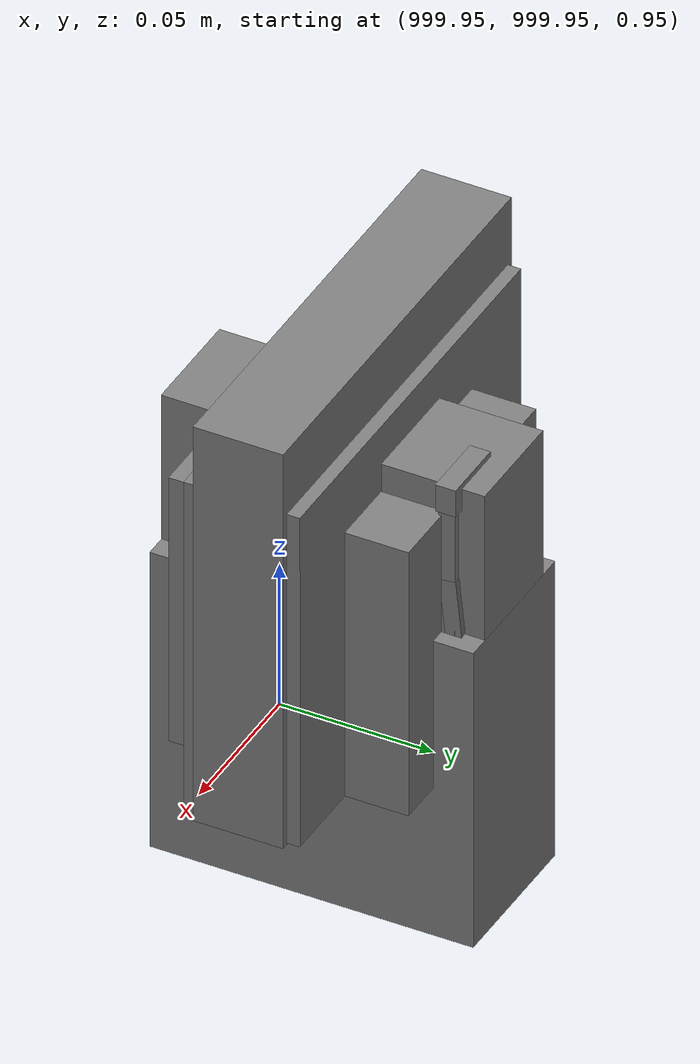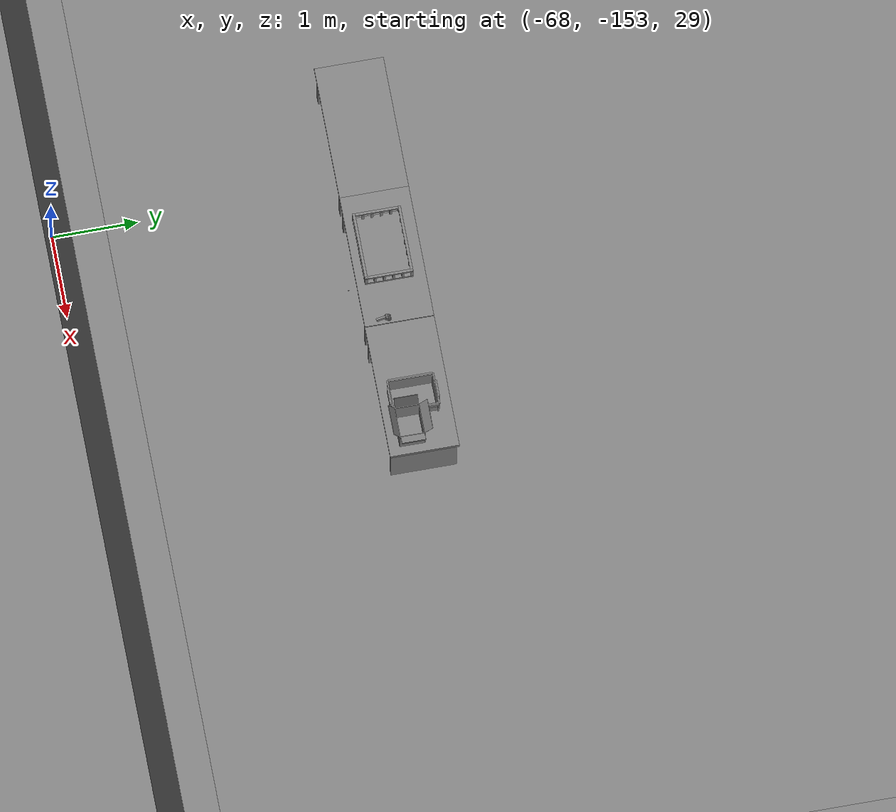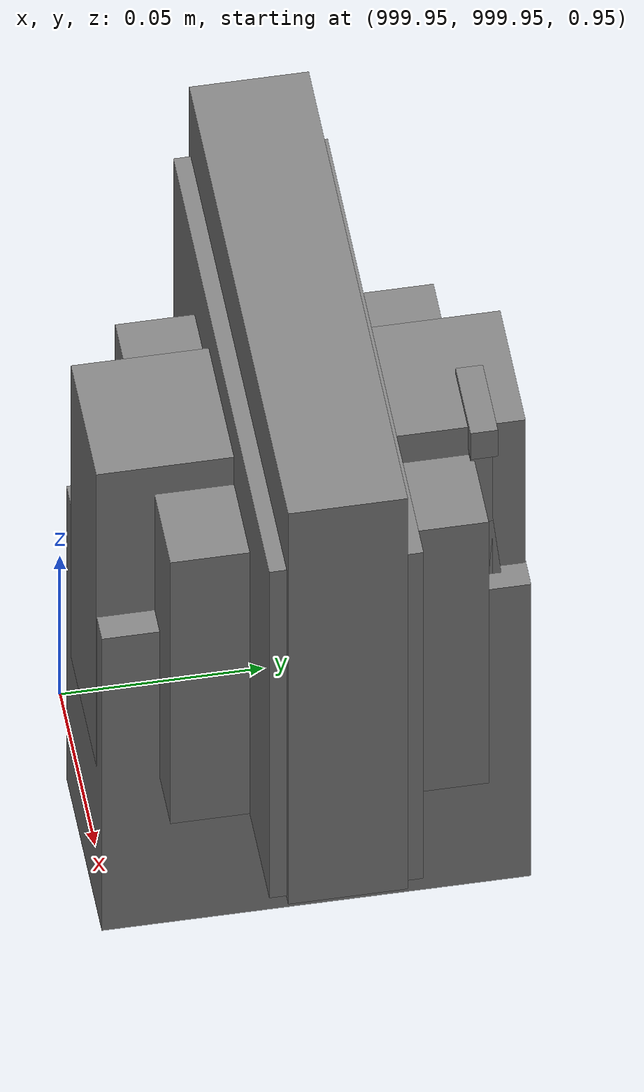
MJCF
<mujoco>
    <option gravity="0.000000000 0.000000000 -9.810000420" timestep="0.0049999999" integrator="implicitfast" density="1.225" viscosity="1.8000001e-05" noslip_iterations="10" iterations="100" sdf_iterations="50">
        <flag multiccd="disable"/>
    </option>
    <size memory="1000M"/>
    <compiler coordinate="local"/>
    <worldbody>
        <light cutoff="30" pos="0 1 1" dir="0 -1 -2"/>
        <light cutoff="30" pos="0 -1 1" dir="0 1 -2"/>
        <body pos="1000.000000000 1000.000000000 1.000000000" euler="0.000000000 0.000000000 180.000000000" name="openloong_gripper_2f85_fix_base_usda_cpu_fan">
            <geom contype="1" conaffinity="1" density="1000" type="box" material="" rgba="0.500000000 0.500000000 0.500000000 1.000000000" solimp="0.899999976 0.949999988 0.001000000" friction="1.000000000 0.005000000 0.000100000" solref="0.020000000 1.000000000" margin="0" condim="3" group="0" pos="0.000000000 0.000000000 0.070034981" quat="0.000000000 0.000000000 0.000000000 1.000000000" size="0.070700005 0.014699999 0.070700005" name="openloong_gripper_2f85_fix_base_usda_geom_4B8DB74D_CA0A_453D_AD03_6BFC076EFDF5"/>
            <freejoint name="openloong_gripper_2f85_fix_base_usda_cpu_fan_joint"/>
            <site size="0.005000000 0.005000000 0.005000000" rgba="0.500000000 0.500000000 0.500000000 1.000000000" pos="0.000000000 0.000000000 0.000000000" quat="0.999961913 0.008726535 0.000000000 0.000000000" group="0" type="sphere" name="openloong_gripper_2f85_fix_base_usda_cpu_fancsite"/>
        </body>
        <body pos="1000.000000000 1000.000000000 1.000000000" euler="0.000000000 0.000000000 180.000000000" name="openloong_gripper_2f85_fix_base_usda_wifi_box">
            <geom contype="1" conaffinity="1" density="1000" type="box" material="" rgba="0.500000000 0.500000000 0.500000000 1.000000000" solimp="0.899999976 0.949999988 0.001000000" friction="1.000000000 0.005000000 0.000100000" solref="0.020000000 1.000000000" margin="0" condim="3" group="0" pos="0.000000000 0.000000000 0.058978677" quat="0.000000000 0.000000047 0.000000000 1.000000000" size="0.068499997 0.018999999 0.059000000" name="openloong_gripper_2f85_fix_base_usda_geom_507A069B_098E_4E4B_A196_973C5524E18D"/>
            <freejoint name="openloong_gripper_2f85_fix_base_usda_wifi_box_joint"/>
            <site size="0.005000000 0.005000000 0.005000000" rgba="0.500000000 0.500000000 0.500000000 1.000000000" pos="0.000000000 0.000000000 0.000000000" quat="0.999961913 0.008726500 0.000000000 0.000000000" group="0" type="sphere" name="openloong_gripper_2f85_fix_base_usda_wifi_boxsite"/>
        </body>
        <body pos="-66.043266296 -149.495788574 31.168247223" euler="-111.256675720 -1.767446518 -41.374828339" mocap="true" name="spotlight6_SpotLight"/>
        <body pos="1000.000000000 1000.000000000 1.000000000" euler="0.000011953 0.000005123 -179.999984741" name="openloong_gripper_2f85_fix_base_usda_intel_box">
            <geom contype="1" conaffinity="1" density="1000" type="box" material="" rgba="0.500000000 0.500000000 0.500000000 1.000000000" solimp="0.899999976 0.949999988 0.001000000" friction="1.000000000 0.005000000 0.000100000" solref="0.020000000 1.000000000" margin="0" condim="3" group="0" pos="0.000000000 -0.000067139 0.000082284" quat="0.707106709 0.000000225 0.000000253 0.707106650" size="0.052800003 0.025300000 0.052800003" name="openloong_gripper_2f85_fix_base_usda_geom_9041334C_7CEA_4C1B_90CD_B1DB6D1EC8CC"/>
            <freejoint name="openloong_gripper_2f85_fix_base_usda_intel_box_joint"/>
            <site size="0.005000000 0.005000000 0.005000000" rgba="0.500000000 0.500000000 0.500000000 1.000000000" pos="0.000000000 0.000000000 0.000000000" quat="0.999961913 0.008726500 0.000000000 0.000000000" group="0" type="sphere" name="openloong_gripper_2f85_fix_base_usda_intel_boxsite"/>
        </body>
        <body pos="1000.000000000 999.999938965 1.000000000" euler="0.000000000 0.000000000 180.000000000" name="openloong_gripper_2f85_fix_base_usda_intelcore_i5">
            <geom contype="1" conaffinity="1" density="1000" type="box" material="" rgba="0.500000000 0.500000000 0.500000000 1.000000000" solimp="0.899999976 0.949999988 0.001000000" friction="1.000000000 0.005000000 0.000100000" solref="0.020000000 1.000000000" margin="0" condim="3" group="0" pos="0.000000000 0.000000000 0.051722717" quat="0.707106709 0.000000000 0.000000000 -0.707106769" size="0.052800000 0.018080002 0.052800000" name="openloong_gripper_2f85_fix_base_usda_geom_EDB29B69_3C9B_493C_B3FD_EB95FAB7678F"/>
            <freejoint name="openloong_gripper_2f85_fix_base_usda_intelcore_i5_joint"/>
            <site size="0.005000000 0.005000000 0.005000000" rgba="0.500000000 0.500000000 0.500000000 1.000000000" pos="0.000000000 0.000000000 0.000000000" quat="0.999961913 0.008726534 0.000000000 0.000000000" group="0" type="sphere" name="openloong_gripper_2f85_fix_base_usda_intelcore_i5site"/>
        </body>
        <body pos="-66.062652588 -149.175567627 31.171895981" euler="21.750366211 60.011028290 124.133628845" mocap="true" name="spotlight3_SpotLight"/>
        <body pos="1000.000000000 1000.000000000 1.000000000" euler="0.000000000 0.000000000 180.000000000" name="openloong_gripper_2f85_fix_base_usda_battery_01">
            <geom contype="1" conaffinity="1" density="1000" type="box" material="" rgba="0.500000000 0.500000000 0.500000000 1.000000000" solimp="0.899999976 0.949999988 0.001000000" friction="1.000000000 0.005000000 0.000100000" solref="0.020000000 1.000000000" margin="0" condim="3" group="0" pos="-0.011123657 -0.041940309 0.101691343" quat="1.000000000 0.000000000 0.000000000 0.000000000" size="0.010800000 0.003375000 0.004725000" name="openloong_gripper_2f85_fix_base_usda_geom_745476F1_DBD2_4F8C_9B8F_7611F342C1E1"/>
            <geom contype="1" conaffinity="1" density="1000" type="box" material="" rgba="0.500000000 0.500000000 0.500000000 1.000000000" solimp="0.899999976 0.949999988 0.001000000" friction="1.000000000 0.005000000 0.000100000" solref="0.020000000 1.000000000" margin="0" condim="3" group="0" pos="-0.010876465 -0.044247437 0.047066893" quat="0.998702705 -0.050920475 0.000000000 0.000000000" size="0.009450001 0.002700000 0.024975000" name="openloong_gripper_2f85_fix_base_usda_geom_0D5915BB_145D_4711_81AC_97CBCFA91BC9"/>
            <geom contype="1" conaffinity="1" density="1000" type="box" material="" rgba="0.500000000 0.500000000 0.500000000 1.000000000" solimp="0.899999976 0.949999988 0.001000000" friction="1.000000000 0.005000000 0.000100000" solref="0.020000000 1.000000000" margin="0" condim="3" group="0" pos="-0.001235962 -0.000659180 0.047381196" quat="1.000000000 0.000000000 0.000000000 0.000000000" size="0.039420001 0.039150000 0.047250003" name="openloong_gripper_2f85_fix_base_usda_geom_E7602802_FA2A_4D94_9BF8_FD0BDC6AEFAC"/>
            <geom contype="1" conaffinity="1" density="1000" type="box" material="" rgba="0.500000000 0.500000000 0.500000000 1.000000000" solimp="0.899999976 0.949999988 0.001000000" friction="1.000000000 0.005000000 0.000100000" solref="0.020000000 1.000000000" margin="0" condim="3" group="0" pos="-0.010876465 -0.039138794 0.009851727" quat="1.000000000 0.000000000 0.000000000 0.000000000" size="0.009450001 0.010800000 0.013500000" name="openloong_gripper_2f85_fix_base_usda_geom_D7915E0C_028D_4975_9570_BA7C3F377D31"/>
            <geom contype="1" conaffinity="1" density="1000" type="box" material="" rgba="0.500000000 0.500000000 0.500000000 1.000000000" solimp="0.899999976 0.949999988 0.001000000" friction="1.000000000 0.005000000 0.000100000" solref="0.020000000 1.000000000" margin="0" condim="3" group="0" pos="-0.010876465 -0.041528322 0.071508206" quat="1.000000000 0.000000000 0.000000000 0.000000000" size="0.009450001 0.002700000 0.027000001" name="openloong_gripper_2f85_fix_base_usda_geom_162887D6_3746_4797_8249_B8DF4D1D1EA3"/>
            <freejoint name="openloong_gripper_2f85_fix_base_usda_battery_01_joint"/>
            <site size="0.005000000 0.005000000 0.005000000" rgba="0.500000000 0.500000000 0.500000000 1.000000000" pos="0.000000000 0.000000000 0.000000000" quat="0.999961913 0.008726500 0.000000000 0.000000000" group="0" type="sphere" name="openloong_gripper_2f85_fix_base_usda_battery_01site"/>
        </body>
        <body pos="-65.967147827 -148.808700562 31.167562485" euler="135.617080688 -32.899597168 -43.356201172" mocap="true" name="spotlight4_SpotLight"/>
        <body pos="-64.866622925 -149.383972168 30.183746338" euler="89.999984741 89.999946594 0.000000000" name="openloong_gripper_2f85_fix_base_usda_bluebox_01">
            <geom contype="1" conaffinity="1" density="1000" type="box" material="" rgba="0.500000000 0.500000000 0.500000000 1.000000000" solimp="0.899999976 0.949999988 0.001000000" friction="1.000000000 0.005000000 0.000100000" solref="0.020000000 1.000000000" margin="0" condim="3" group="0" pos="0.276580811 0.187225342 0.000068665" quat="0.707106948 0.000077471 0.707106352 0.000077486" size="0.100000001 0.057999998 0.010000000" name="openloong_gripper_2f85_fix_base_usda_geom_03EC9B35_0254_4B4F_B4E3_D238617670E5"/>
            <geom contype="1" conaffinity="1" density="1000" type="box" material="" rgba="0.500000000 0.500000000 0.500000000 1.000000000" solimp="0.899999976 0.949999988 0.001000000" friction="1.000000000 0.005000000 0.000100000" solref="0.020000000 1.000000000" margin="0" condim="3" group="0" pos="0.000000000 0.002883911 0.000000000" quat="0.999999881 0.000000000 0.000000000 0.000000000" size="0.254000008 0.003000000 0.172000006" name="openloong_gripper_2f85_fix_base_usda_geom_1F9ED6B9_13D7_4B46_9649_4DA44CC16DE7"/>
            <geom contype="1" conaffinity="1" density="1000" type="box" material="" rgba="0.500000000 0.500000000 0.500000000 1.000000000" solimp="0.899999976 0.949999988 0.001000000" friction="1.000000000 0.005000000 0.000100000" solref="0.020000000 1.000000000" margin="0" condim="3" group="0" pos="0.000000000 0.124874115 0.173484802" quat="0.999796331 0.020176515 -0.000000015 0.000000030" size="0.259999990 0.119999997 0.007000000" name="openloong_gripper_2f85_fix_base_usda_geom_CC26214E_EA8F_4436_B214_DF3E03568A88"/>
            <geom contype="1" conaffinity="1" density="1000" type="box" material="" rgba="0.500000000 0.500000000 0.500000000 1.000000000" solimp="0.899999976 0.949999988 0.001000000" friction="1.000000000 0.005000000 0.000100000" solref="0.020000000 1.000000000" margin="0" condim="3" group="0" pos="0.000000000 0.124874115 -0.173469543" quat="0.999796331 -0.020176545 -0.000000015 0.000000000" size="0.259999990 0.119999997 0.007000000" name="openloong_gripper_2f85_fix_base_usda_geom_8D0857D8_8AE9_4B1B_8EE8_ED49C5E44F52"/>
            <geom contype="1" conaffinity="1" density="1000" type="box" material="" rgba="0.500000000 0.500000000 0.500000000 1.000000000" solimp="0.899999976 0.949999988 0.001000000" friction="1.000000000 0.005000000 0.000100000" solref="0.020000000 1.000000000" margin="0" condim="3" group="0" pos="0.000000000 0.214008331 0.188980103" quat="0.999912977 0.013176724 0.000000015 0.000000000" size="0.259999990 0.029999999 0.012500000" name="openloong_gripper_2f85_fix_base_usda_geom_B69DC583_C818_4B3B_88C4_5E33191A58AA"/>
            <geom contype="1" conaffinity="1" density="1000" type="box" material="" rgba="0.500000000 0.500000000 0.500000000 1.000000000" solimp="0.899999976 0.949999988 0.001000000" friction="1.000000000 0.005000000 0.000100000" solref="0.020000000 1.000000000" margin="0" condim="3" group="0" pos="-0.258361816 0.125289917 0.001876831" quat="0.702796936 -0.020792112 0.710783124 0.020769298" size="0.189999998 0.119999997 0.009000000" name="openloong_gripper_2f85_fix_base_usda_geom_D8AB7E4B_4CF2_4605_86FC_1DF68866EEC6"/>
            <geom contype="1" conaffinity="1" density="1000" type="box" material="" rgba="0.500000000 0.500000000 0.500000000 1.000000000" solimp="0.899999976 0.949999988 0.001000000" friction="1.000000000 0.005000000 0.000100000" solref="0.020000000 1.000000000" margin="0" condim="3" group="0" pos="0.000000000 0.214008331 -0.188980103" quat="0.999912977 -0.013176769 0.000000030 0.000000015" size="0.259999990 0.029999999 0.012500000" name="openloong_gripper_2f85_fix_base_usda_geom_172F6388_4D0A_4259_B265_2D69C002F59A"/>
            <geom contype="1" conaffinity="1" density="1000" type="box" material="" rgba="0.500000000 0.500000000 0.500000000 1.000000000" solimp="0.899999976 0.949999988 0.001000000" friction="1.000000000 0.005000000 0.000100000" solref="0.020000000 1.000000000" margin="0" condim="3" group="0" pos="-0.276611328 0.187225342 0.000068665" quat="0.707106650 0.000077441 0.707106709 0.000077456" size="0.100000001 0.057999998 0.010000000" name="openloong_gripper_2f85_fix_base_usda_geom_AAB85F67_C1DA_4951_9484_A152460C22E3"/>
            <geom contype="1" conaffinity="1" density="1000" type="box" material="" rgba="0.500000000 0.500000000 0.500000000 1.000000000" solimp="0.899999976 0.949999988 0.001000000" friction="1.000000000 0.005000000 0.000100000" solref="0.020000000 1.000000000" margin="0" condim="3" group="0" pos="0.258331299 0.125289917 0.001876831" quat="0.702851415 0.018856421 0.710823774 -0.019329369" size="0.189999998 0.119999997 0.009000000" name="openloong_gripper_2f85_fix_base_usda_geom_6B8CC07A_562B_4734_9ED8_E2C01A44747A"/>
            <freejoint name="openloong_gripper_2f85_fix_base_usda_bluebox_01_joint"/>
            <site size="0.005000000 0.005000000 0.005000000" rgba="0.500000000 0.500000000 0.500000000 1.000000000" pos="0.000000000 0.000000000 0.000000000" quat="0.999961913 0.008726534 0.000000000 0.000000000" group="0" type="sphere" name="openloong_gripper_2f85_fix_base_usda_bluebox_01site"/>
        </body>
        <body pos="-64.496299744 -149.491867065 30.235729218" euler="0.000000000 0.000000000 89.999946594" name="openloong_gripper_2f85_fix_base_usda_cardboardbox_01">
            <geom contype="1" conaffinity="1" density="1000" type="box" material="" rgba="0.500000000 0.500000000 0.500000000 1.000000000" solimp="0.899999976 0.949999988 0.001000000" friction="1.000000000 0.005000000 0.000100000" solref="0.020000000 1.000000000" margin="0" condim="3" group="0" pos="-0.003166199 -0.004086494 0.005052090" quat="1.000000000 0.000000000 0.000000000 0.000000000" size="0.142499998 0.177500010 0.005000000" name="openloong_gripper_2f85_fix_base_usda_geom_C274832E_FCD5_4EF1_A975_35A4B53EBE39"/>
            <geom contype="1" conaffinity="1" density="1000" type="box" material="" rgba="0.500000000 0.500000000 0.500000000 1.000000000" solimp="0.899999976 0.949999988 0.001000000" friction="1.000000000 0.005000000 0.000100000" solref="0.020000000 1.000000000" margin="0" condim="3" group="0" pos="-0.003166199 0.170316696 0.150570869" quat="1.000000000 0.000000000 0.000000000 0.000000000" size="0.142499998 0.005000000 0.149999991" name="openloong_gripper_2f85_fix_base_usda_geom_BB88E222_F462_4A00_A6F0_D6824A2208F5"/>
            <geom contype="1" conaffinity="1" density="1000" type="box" material="" rgba="0.500000000 0.500000000 0.500000000 1.000000000" solimp="0.899999976 0.949999988 0.001000000" friction="1.000000000 0.005000000 0.000100000" solref="0.020000000 1.000000000" margin="0" condim="3" group="0" pos="-0.147399902 -0.005307198 0.150570869" quat="1.000000000 0.000000000 0.000000000 0.000000000" size="0.005000000 0.177500010 0.149999991" name="openloong_gripper_2f85_fix_base_usda_geom_97BA49CB_9E7E_434D_B408_3A2F80ACFDCA"/>
            <geom contype="1" conaffinity="1" density="1000" type="box" material="" rgba="0.500000000 0.500000000 0.500000000 1.000000000" solimp="0.899999976 0.949999988 0.001000000" friction="1.000000000 0.005000000 0.000100000" solref="0.020000000 1.000000000" margin="0" condim="3" group="0" pos="0.140275955 -0.005307198 0.150570869" quat="1.000000000 0.000000000 0.000000000 0.000000000" size="0.005000000 0.177500010 0.149999991" name="openloong_gripper_2f85_fix_base_usda_geom_D86E874D_BFA9_484A_9D1A_D29EECF638F0"/>
            <geom contype="1" conaffinity="1" density="1000" type="box" material="" rgba="0.500000000 0.500000000 0.500000000 1.000000000" solimp="0.899999976 0.949999988 0.001000000" friction="1.000000000 0.005000000 0.000100000" solref="0.020000000 1.000000000" margin="0" condim="3" group="0" pos="-0.003166199 -0.181550980 0.150570869" quat="1.000000000 0.000000000 0.000000000 0.000000000" size="0.142499998 0.005000000 0.149999991" name="openloong_gripper_2f85_fix_base_usda_geom_63989445_84C4_492D_9C8D_C1A08963AA8C"/>
            <freejoint name="openloong_gripper_2f85_fix_base_usda_cardboardbox_01_joint"/>
            <site size="0.005000000 0.005000000 0.005000000" rgba="0.500000000 0.500000000 0.500000000 1.000000000" pos="0.000000000 0.000000000 0.000000000" quat="0.999961913 0.008726535 0.000000000 0.000000000" group="0" type="sphere" name="openloong_gripper_2f85_fix_base_usda_site_6772CCFF_6FC9_4B57_AA38_137CAADC3AAD"/>
            <body pos="0.139160156 -0.004048347 0.301930904" euler="-179.999954224 49.383502960 179.999954224" name="openloong_gripper_2f85_fix_base_usda_A1_006">
                <geom contype="1" conaffinity="1" density="1000" type="box" material="" rgba="0.500000000 0.500000000 0.500000000 1.000000000" solimp="0.899999976 0.949999988 0.001000000" friction="1.000000000 0.005000000 0.000100000" solref="0.020000000 1.000000000" margin="0" condim="3" group="0" pos="-0.071587563 0.000009537 0.001745224" quat="0.999999881 0.000000000 0.000000000 0.000000000" size="0.071249999 0.179999992 0.002500000" name="openloong_gripper_2f85_fix_base_usda_geom_00651533_498F_4E66_8540_EB70A6A49F88"/>
                <joint armature="0" stiffness="0.07" damping="0.0099999998" axis="0.000000 1.000000 0.000000" type="hinge" name="openloong_gripper_2f85_fix_base_usda_A1_006"/>
            </body>
            <body pos="-0.145902634 -0.004086494 0.301938057" euler="-180.000000000 -60.000011444 -180.000000000" name="openloong_gripper_2f85_fix_base_usda_A2_006">
                <geom contype="1" conaffinity="1" density="1000" type="box" material="" rgba="0.500000000 0.500000000 0.500000000 1.000000000" solimp="0.899999976 0.949999988 0.001000000" friction="1.000000000 0.005000000 0.000100000" solref="0.020000000 1.000000000" margin="0" condim="3" group="0" pos="0.071268082 0.000009537 0.002717972" quat="0.000002921 0.000000000 -0.000000030 0.999999881" size="0.071249999 0.179999992 0.002500000" name="openloong_gripper_2f85_fix_base_usda_geom_F5C0D898_6E57_4F5A_9478_3FC617235B50"/>
                <joint armature="0" stiffness="0.07" damping="0.0099999998" axis="0.000000 1.000000 0.000000" type="hinge" name="openloong_gripper_2f85_fix_base_usda_A2_006"/>
            </body>
            <body pos="-0.003385544 0.175991058 0.301930904" euler="-125.858116150 -0.000004561 0.000002331" name="openloong_gripper_2f85_fix_base_usda_B2_006">
                <geom contype="1" conaffinity="1" density="1000" type="box" material="" rgba="0.500000000 0.500000000 0.500000000 1.000000000" solimp="0.899999976 0.949999988 0.001000000" friction="1.000000000 0.005000000 0.000100000" solref="0.020000000 1.000000000" margin="0" condim="3" group="0" pos="0.000009537 -0.070939064 -0.002470016" quat="0.999614120 0.027776197 -0.000000015 0.000000030" size="0.137500003 0.064999998 0.005000000" name="openloong_gripper_2f85_fix_base_usda_geom_33967E3F_2AA0_47B1_9B11_31313E116A6E"/>
                <joint armature="0" stiffness="0.07" damping="0.0099999998" axis="1.000000 0.000000 0.000000" type="hinge" name="openloong_gripper_2f85_fix_base_usda_B2_006"/>
            </body>
            <body pos="-0.003385544 -0.184140205 0.301938057" euler="147.805557251 0.000000000 0.000000000" name="openloong_gripper_2f85_fix_base_usda_B1_006">
                <geom contype="1" conaffinity="1" density="1000" type="box" material="" rgba="0.500000000 0.500000000 0.500000000 1.000000000" solimp="0.899999976 0.949999988 0.001000000" friction="1.000000000 0.005000000 0.000100000" solref="0.020000000 1.000000000" margin="0" condim="3" group="0" pos="-0.000028610 0.070202351 -0.002703667" quat="0.999614179 -0.027776167 0.000000000 0.000000000" size="0.137500003 0.064999998 0.005000000" name="openloong_gripper_2f85_fix_base_usda_geom_B5B6D863_A356_477A_9E13_78ADF58D6AC8"/>
                <joint armature="0" stiffness="0.07" damping="0.0099999998" axis="1.000000 0.000000 0.000000" type="hinge" name="openloong_gripper_2f85_fix_base_usda_B1_006"/>
            </body>
        </body>
        <body pos="-65.882858276 -149.481979370 30.229999542" euler="-64.487716675 0.000000000 0.000000000" name="openloong_gripper_2f85_fix_base_usda_Barcode">
            <geom contype="1" conaffinity="1" density="1000" type="box" material="" rgba="0.500000000 0.500000000 0.500000000 1.000000000" solimp="0.899999976 0.949999988 0.001000000" friction="1.000000000 0.005000000 0.000100000" solref="0.020000000 1.000000000" margin="0" condim="3" group="0" pos="0.000000000 0.013038635 0.001419067" quat="0.000000000 0.000000000 0.000000000 1.000000119" size="0.034000002 0.010000000 0.017999999" name="openloong_gripper_2f85_fix_base_usda_geom_937252F1_E8C2_49E2_B22A_832AB5A50097"/>
            <geom contype="1" conaffinity="1" density="1000" type="box" material="" rgba="0.500000000 0.500000000 0.500000000 1.000000000" solimp="0.899999976 0.949999988 0.001000000" friction="1.000000000 0.005000000 0.000100000" solref="0.020000000 1.000000000" margin="0" condim="3" group="0" pos="0.000000000 -0.035301208 -0.007095337" quat="0.000000000 0.000000000 -0.043619365 0.999048233" size="0.028999999 0.010000000 0.020000000" name="openloong_gripper_2f85_fix_base_usda_geom_68268379_102C_4007_B4E3_1FF096D39834"/>
            <geom contype="1" conaffinity="1" density="1000" type="box" material="" rgba="0.500000000 0.500000000 0.500000000 1.000000000" solimp="0.899999976 0.949999988 0.001000000" friction="1.000000000 0.005000000 0.000100000" solref="0.020000000 1.000000000" margin="0" condim="3" group="0" pos="0.000000000 -0.043411255 -0.011749268" quat="0.922262907 0.386563420 0.000000000 0.000000000" size="0.026000001 0.010000000 0.020000000" name="openloong_gripper_2f85_fix_base_usda_geom_AE79179D_0E00_4833_A8F4_E5F943131B3A"/>
            <geom contype="1" conaffinity="1" density="1000" type="box" material="" rgba="0.500000000 0.500000000 0.500000000 1.000000000" solimp="0.899999976 0.949999988 0.001000000" friction="1.000000000 0.005000000 0.000100000" solref="0.020000000 1.000000000" margin="0" condim="3" group="0" pos="0.000000000 -0.016967773 -0.031860352" quat="0.000000000 0.000000000 0.000000000 1.000000119" size="0.008000000 0.010000000 0.013000000" name="openloong_gripper_2f85_fix_base_usda_geom_65BAEC24_FFDA_4120_814D_50BBB5100EF0"/>
            <geom contype="1" conaffinity="1" density="1000" type="box" material="" rgba="0.500000000 0.500000000 0.500000000 1.000000000" solimp="0.899999976 0.949999988 0.001000000" friction="1.000000000 0.005000000 0.000100000" solref="0.020000000 1.000000000" margin="0" condim="3" group="0" pos="0.000000000 -0.001869202 0.000312805" quat="0.953716993 0.300705761 0.000000000 0.000000000" size="0.032000002 0.010000000 0.018999999" name="openloong_gripper_2f85_fix_base_usda_geom_D89F22BC_65C4_42F6_B28F_129F4EC49B57"/>
            <geom contype="1" conaffinity="1" density="1000" type="box" material="" rgba="0.500000000 0.500000000 0.500000000 1.000000000" solimp="0.899999976 0.949999988 0.001000000" friction="1.000000000 0.005000000 0.000100000" solref="0.020000000 1.000000000" margin="0" condim="3" group="0" pos="0.000000000 -0.019531250 -0.003173828" quat="0.953716993 0.300705761 0.000000000 0.000000000" size="0.030999999 0.010000000 0.020000000" name="openloong_gripper_2f85_fix_base_usda_geom_4C687536_8822_4D5F_9845_C929034AB78A"/>
            <geom contype="1" conaffinity="1" density="1000" type="box" material="" rgba="0.500000000 0.500000000 0.500000000 1.000000000" solimp="0.899999976 0.949999988 0.001000000" friction="1.000000000 0.005000000 0.000100000" solref="0.020000000 1.000000000" margin="0" condim="3" group="0" pos="0.000000000 -0.035301208 -0.007095337" quat="0.953716993 0.300705761 0.000000000 0.000000000" size="0.028999999 0.010000000 0.020000000" name="openloong_gripper_2f85_fix_base_usda_geom_CBB40982_EA32_45AA_8551_3A667EBB7F69"/>
            <geom contype="1" conaffinity="1" density="1000" type="box" material="" rgba="0.500000000 0.500000000 0.500000000 1.000000000" solimp="0.899999976 0.949999988 0.001000000" friction="1.000000000 0.005000000 0.000100000" solref="0.020000000 1.000000000" margin="0" condim="3" group="0" pos="0.000000000 -0.042617798 -0.071121216" quat="0.000000000 0.000000000 0.000000000 1.000000119" size="0.013000000 0.021000000 0.059999999" name="openloong_gripper_2f85_fix_base_usda_geom_681914BA_8783_4C2B_9D91_154435EC0880"/>
            <freejoint name="openloong_gripper_2f85_fix_base_usda_Barcode_joint"/>
            <site size="0.005000000 0.005000000 0.005000000" rgba="0.500000000 0.500000000 0.500000000 1.000000000" pos="0.000000000 0.000000000 0.000000000" quat="1.000000000 0.000000000 0.000000000 0.000000000" group="0" type="sphere" name="openloong_gripper_2f85_fix_base_usda_Barcode_site"/>
        </body>
        <body pos="-66.745018005 -149.392349243 30.184000015" euler="0.000000000 0.000000000 89.999946594" name="[22330358983145]_Basket_01">
            <geom contype="1" conaffinity="1" density="1000" type="box" material="" rgba="0.500000000 0.500000000 0.500000000 1.000000000" solimp="0.899999976 0.949999988 0.001000000" friction="1.000000000 0.005000000 0.000100000" solref="0.020000000 1.000000000" margin="0" condim="3" group="0" pos="-0.052425385 0.389207840 0.089787483" quat="0.707107008 0.000000000 0.000000000 0.707106411" size="0.014249999 0.014249999 0.059999999" name="[22330358983145]_geom_BDBD9274_908C_481A_9F20_E6A91EF9C626"/>
            <geom contype="1" conaffinity="1" density="1000" type="box" material="" rgba="0.500000000 0.500000000 0.500000000 1.000000000" solimp="0.899999976 0.949999988 0.001000000" friction="1.000000000 0.005000000 0.000100000" solref="0.020000000 1.000000000" margin="0" condim="3" group="0" pos="0.264015198 -0.133043289 0.089787483" quat="0.707107008 0.000000000 0.000000000 0.707106411" size="0.014249999 0.014249999 0.059999999" name="[22330358983145]_geom_233A49B9_1F94_43E4_9B7D_3A63AB3C2993"/>
            <geom contype="1" conaffinity="1" density="1000" type="box" material="" rgba="0.500000000 0.500000000 0.500000000 1.000000000" solimp="0.899999976 0.949999988 0.001000000" friction="1.000000000 0.005000000 0.000100000" solref="0.020000000 1.000000000" margin="0" condim="3" group="0" pos="-0.264015198 -0.265548706 0.089793205" quat="0.707107008 0.000000000 0.000000000 0.707106411" size="0.014249999 0.014249999 0.059999999" name="[22330358983145]_geom_70ACE54F_1052_4A3F_871C_4206311DE43F"/>
            <geom contype="1" conaffinity="1" density="1000" type="box" material="" rgba="0.500000000 0.500000000 0.500000000 1.000000000" solimp="0.899999976 0.949999988 0.001000000" friction="1.000000000 0.005000000 0.000100000" solref="0.020000000 1.000000000" margin="0" condim="3" group="0" pos="-0.160263062 -0.389322281 0.089793205" quat="0.707107008 0.000000000 0.000000000 0.707106411" size="0.014249999 0.014249999 0.059999999" name="[22330358983145]_geom_BC363D5E_181F_4E01_A705_39C734D925DF"/>
            <geom contype="1" conaffinity="1" density="1000" type="box" material="" rgba="0.500000000 0.500000000 0.500000000 1.000000000" solimp="0.899999976 0.949999988 0.001000000" friction="1.000000000 0.005000000 0.000100000" solref="0.020000000 1.000000000" margin="0" condim="3" group="0" pos="0.162265778 -0.389322281 0.089787483" quat="0.707107008 0.000000000 0.000000000 0.707106411" size="0.014249999 0.014249999 0.059999999" name="[22330358983145]_geom_AB3AAEFE_BB0B_41E6_8B23_5E613F9563F2"/>
            <geom contype="1" conaffinity="1" density="1000" type="box" material="" rgba="0.500000000 0.500000000 0.500000000 1.000000000" solimp="0.899999976 0.949999988 0.001000000" friction="1.000000000 0.005000000 0.000100000" solref="0.020000000 1.000000000" margin="0" condim="3" group="0" pos="0.264015198 0.389207840 0.089787483" quat="0.707107008 0.000000000 0.000000000 0.707106411" size="0.014249999 0.014249999 0.059999999" name="[22330358983145]_geom_BB2F9C39_BE3E_447D_B24C_5FBD66DED10F"/>
            <geom contype="1" conaffinity="1" density="1000" type="box" material="" rgba="0.500000000 0.500000000 0.500000000 1.000000000" solimp="0.899999976 0.949999988 0.001000000" friction="1.000000000 0.005000000 0.000100000" solref="0.020000000 1.000000000" margin="0" condim="3" group="0" pos="-0.264015198 -0.133043289 0.089793205" quat="0.707107008 0.000000000 0.000000000 0.707106411" size="0.014249999 0.014249999 0.059999999" name="[22330358983145]_geom_CE4291DA_CF67_454B_B64A_11111EB425F0"/>
            <geom contype="1" conaffinity="1" density="1000" type="box" material="" rgba="0.500000000 0.500000000 0.500000000 1.000000000" solimp="0.899999976 0.949999988 0.001000000" friction="1.000000000 0.005000000 0.000100000" solref="0.020000000 1.000000000" margin="0" condim="3" group="0" pos="-0.264026642 0.269256592 0.089793205" quat="0.707107008 0.000000000 0.000000000 0.707106411" size="0.014249999 0.014249999 0.059999999" name="[22330358983145]_geom_3EB86688_12FB_4FD1_B23B_72545A878482"/>
            <geom contype="1" conaffinity="1" density="1000" type="box" material="" rgba="0.500000000 0.500000000 0.500000000 1.000000000" solimp="0.899999976 0.949999988 0.001000000" friction="1.000000000 0.005000000 0.000100000" solref="0.020000000 1.000000000" margin="0" condim="3" group="0" pos="0.054462433 0.389207840 0.089787483" quat="0.707107008 0.000000000 0.000000000 0.707106411" size="0.014249999 0.014249999 0.059999999" name="[22330358983145]_geom_61BA44CA_0785_4DAA_B2C2_4F954EFF48A3"/>
            <geom contype="1" conaffinity="1" density="1000" type="box" material="" rgba="0.500000000 0.500000000 0.500000000 1.000000000" solimp="0.899999976 0.949999988 0.001000000" friction="1.000000000 0.005000000 0.000100000" solref="0.020000000 1.000000000" margin="0" condim="3" group="0" pos="0.054462433 -0.389322281 0.089787483" quat="0.707107008 0.000000000 0.000000000 0.707106411" size="0.014249999 0.014249999 0.059999999" name="[22330358983145]_geom_7F334F34_7D3B_4F24_831A_642DD3039CA2"/>
            <geom contype="1" conaffinity="1" density="1000" type="box" material="" rgba="0.500000000 0.500000000 0.500000000 1.000000000" solimp="0.899999976 0.949999988 0.001000000" friction="1.000000000 0.005000000 0.000100000" solref="0.020000000 1.000000000" margin="0" condim="3" group="0" pos="0.264015198 0.269256592 0.089793205" quat="0.707107008 0.000000000 0.000000000 0.707106411" size="0.014249999 0.014249999 0.059999999" name="[22330358983145]_geom_A6D891D0_69D6_43F9_8961_0DCCC0C126DB"/>
            <geom contype="1" conaffinity="1" density="1000" type="box" material="" rgba="0.500000000 0.500000000 0.500000000 1.000000000" solimp="0.899999976 0.949999988 0.001000000" friction="1.000000000 0.005000000 0.000100000" solref="0.020000000 1.000000000" margin="0" condim="3" group="0" pos="0.264015198 -0.389322281 0.089787483" quat="0.707107008 0.000000000 0.000000000 0.707106411" size="0.014249999 0.014249999 0.059999999" name="[22330358983145]_geom_3816E6E2_DDAF_4A76_ABA7_5A9BD6DC320D"/>
            <geom contype="1" conaffinity="1" density="1000" type="box" material="" rgba="0.500000000 0.500000000 0.500000000 1.000000000" solimp="0.899999976 0.949999988 0.001000000" friction="1.000000000 0.005000000 0.000100000" solref="0.020000000 1.000000000" margin="0" condim="3" group="0" pos="0.000000000 0.000000000 0.015998840" quat="0.707107008 0.000000000 0.000000000 0.707106411" size="0.403499991 0.279000014 0.015750000" name="[22330358983145]_geom_A04BECBF_F06D_4D6E_A8D3_3427A895A58D"/>
            <geom contype="1" conaffinity="1" density="1000" type="box" material="" rgba="0.500000000 0.500000000 0.500000000 1.000000000" solimp="0.899999976 0.949999988 0.001000000" friction="1.000000000 0.005000000 0.000100000" solref="0.020000000 1.000000000" margin="0" condim="3" group="0" pos="0.000000000 -0.389476776 0.163619041" quat="0.707107008 0.000000000 0.000000000 0.707106411" size="0.015000000 0.277500004 0.015750000" name="[22330358983145]_geom_4D7E0B16_6976_4A93_9116_15AB9748A791"/>
            <geom contype="1" conaffinity="1" density="1000" type="box" material="" rgba="0.500000000 0.500000000 0.500000000 1.000000000" solimp="0.899999976 0.949999988 0.001000000" friction="1.000000000 0.005000000 0.000100000" solref="0.020000000 1.000000000" margin="0" condim="3" group="0" pos="0.162265778 0.389207840 0.089787483" quat="0.707107008 0.000000000 0.000000000 0.707106411" size="0.014249999 0.014249999 0.059999999" name="[22330358983145]_geom_CBA91365_C494_4567_A17C_7C73EAB00DDC"/>
            <geom contype="1" conaffinity="1" density="1000" type="box" material="" rgba="0.500000000 0.500000000 0.500000000 1.000000000" solimp="0.899999976 0.949999988 0.001000000" friction="1.000000000 0.005000000 0.000100000" solref="0.020000000 1.000000000" margin="0" condim="3" group="0" pos="0.000000000 0.389471054 0.163619041" quat="0.707107008 0.000000000 0.000000000 0.707106411" size="0.015000000 0.277500004 0.015750000" name="[22330358983145]_geom_84992256_40F8_4F60_8C63_B525220DE7E5"/>
            <geom contype="1" conaffinity="1" density="1000" type="box" material="" rgba="0.500000000 0.500000000 0.500000000 1.000000000" solimp="0.899999976 0.949999988 0.001000000" friction="1.000000000 0.005000000 0.000100000" solref="0.020000000 1.000000000" margin="0" condim="3" group="0" pos="-0.263511658 0.000000000 0.163619041" quat="0.707107008 0.000000000 0.000000000 0.707106411" size="0.403499991 0.015000000 0.015750000" name="[22330358983145]_geom_9452F5C4_760B_4C1B_AB58_FDD1CE8503FD"/>
            <geom contype="1" conaffinity="1" density="1000" type="box" material="" rgba="0.500000000 0.500000000 0.500000000 1.000000000" solimp="0.899999976 0.949999988 0.001000000" friction="1.000000000 0.005000000 0.000100000" solref="0.020000000 1.000000000" margin="0" condim="3" group="0" pos="-0.264015198 0.141334534 0.089793205" quat="0.707107008 0.000000000 0.000000000 0.707106411" size="0.014249999 0.014249999 0.059999999" name="[22330358983145]_geom_EA5580F4_DC75_462E_9F96_6EDA48312439"/>
            <geom contype="1" conaffinity="1" density="1000" type="box" material="" rgba="0.500000000 0.500000000 0.500000000 1.000000000" solimp="0.899999976 0.949999988 0.001000000" friction="1.000000000 0.005000000 0.000100000" solref="0.020000000 1.000000000" margin="0" condim="3" group="0" pos="0.264015198 -0.265548706 0.089787483" quat="0.707107008 0.000000000 0.000000000 0.707106411" size="0.014249999 0.014249999 0.059999999" name="[22330358983145]_geom_BE668007_68DE_4EC7_8D68_F0FC28C5B768"/>
            <geom contype="1" conaffinity="1" density="1000" type="box" material="" rgba="0.500000000 0.500000000 0.500000000 1.000000000" solimp="0.899999976 0.949999988 0.001000000" friction="1.000000000 0.005000000 0.000100000" solref="0.020000000 1.000000000" margin="0" condim="3" group="0" pos="-0.160263062 0.389207840 0.089787483" quat="0.707107008 0.000000000 0.000000000 0.707106411" size="0.014249999 0.014249999 0.059999999" name="[22330358983145]_geom_6514BBC6_2269_400A_ABAA_E6306428F087"/>
            <geom contype="1" conaffinity="1" density="1000" type="box" material="" rgba="0.500000000 0.500000000 0.500000000 1.000000000" solimp="0.899999976 0.949999988 0.001000000" friction="1.000000000 0.005000000 0.000100000" solref="0.020000000 1.000000000" margin="0" condim="3" group="0" pos="-0.052425385 -0.389322281 0.089787483" quat="0.707107008 0.000000000 0.000000000 0.707106411" size="0.014249999 0.014249999 0.059999999" name="[22330358983145]_geom_8F681B2D_8D5A_42DE_9718_D7F236D6F011"/>
            <geom contype="1" conaffinity="1" density="1000" type="box" material="" rgba="0.500000000 0.500000000 0.500000000 1.000000000" solimp="0.899999976 0.949999988 0.001000000" friction="1.000000000 0.005000000 0.000100000" solref="0.020000000 1.000000000" margin="0" condim="3" group="0" pos="-0.264026642 -0.389322281 0.089793205" quat="0.707107008 0.000000000 0.000000000 0.707106411" size="0.014249999 0.014249999 0.059999999" name="[22330358983145]_geom_D2C7F53A_58E6_451D_9A51_E0F9BAA0FCA6"/>
            <geom contype="1" conaffinity="1" density="1000" type="box" material="" rgba="0.500000000 0.500000000 0.500000000 1.000000000" solimp="0.899999976 0.949999988 0.001000000" friction="1.000000000 0.005000000 0.000100000" solref="0.020000000 1.000000000" margin="0" condim="3" group="0" pos="0.264015198 0.141334534 0.089787483" quat="0.707107008 0.000000000 0.000000000 0.707106411" size="0.014249999 0.014249999 0.059999999" name="[22330358983145]_geom_3FE828D4_61FF_4A7B_BE97_B71AC01C87DD"/>
            <geom contype="1" conaffinity="1" density="1000" type="box" material="" rgba="0.500000000 0.500000000 0.500000000 1.000000000" solimp="0.899999976 0.949999988 0.001000000" friction="1.000000000 0.005000000 0.000100000" solref="0.020000000 1.000000000" margin="0" condim="3" group="0" pos="-0.264015198 0.389207840 0.089793205" quat="0.707107008 0.000000000 0.000000000 0.707106411" size="0.014249999 0.014249999 0.059999999" name="[22330358983145]_geom_1225620A_1BFE_4DAC_A7FF_C3A1AC0D1459"/>
            <geom contype="1" conaffinity="1" density="1000" type="box" material="" rgba="0.500000000 0.500000000 0.500000000 1.000000000" solimp="0.899999976 0.949999988 0.001000000" friction="1.000000000 0.005000000 0.000100000" solref="0.020000000 1.000000000" margin="0" condim="3" group="0" pos="0.264015198 0.004480362 0.089787483" quat="0.707107008 0.000000000 0.000000000 0.707106411" size="0.014249999 0.014249999 0.059999999" name="[22330358983145]_geom_CDA03FBD_828A_477F_B3DA_2524BFEC6196"/>
            <geom contype="1" conaffinity="1" density="1000" type="box" material="" rgba="0.500000000 0.500000000 0.500000000 1.000000000" solimp="0.899999976 0.949999988 0.001000000" friction="1.000000000 0.005000000 0.000100000" solref="0.020000000 1.000000000" margin="0" condim="3" group="0" pos="0.263694763 -0.000011444 0.163619041" quat="0.707107008 0.000000000 0.000000000 0.707106411" size="0.403499991 0.015000000 0.015750000" name="[22330358983145]_geom_C1B57ED3_35BA_48E9_82BC_A2C91BAEE494"/>
            <geom contype="1" conaffinity="1" density="1000" type="box" material="" rgba="0.500000000 0.500000000 0.500000000 1.000000000" solimp="0.899999976 0.949999988 0.001000000" friction="1.000000000 0.005000000 0.000100000" solref="0.020000000 1.000000000" margin="0" condim="3" group="0" pos="-0.264015198 0.004480362 0.089793205" quat="0.707107008 0.000000000 0.000000000 0.707106411" size="0.014249999 0.014249999 0.059999999" name="[22330358983145]_geom_21DDA4CE_E787_416F_A08C_A164BA197396"/>
            <freejoint name="[22330358983145]_joint_7D51934A_6448_4C91_9709_11E166CD0A80"/>
        </body>
        <body pos="0.000000000 0.000000000 0.000000000" euler="0.000000000 0.000000000 0.000000000" name="Static Objects_Static Objects">
            <geom contype="1" conaffinity="1" density="1000" type="box" material="" rgba="0.500000000 0.500000000 0.500000000 1.000000000" solimp="0.899999976 0.949999988 0.001000000" friction="1.000000000 0.005000000 0.000100000" solref="0.020000000 1.000000000" margin="0" condim="3" group="0" pos="-67.544113159 -149.365814209 29.727830887" quat="0.500000417 0.499999970 0.499999553 0.499999970" size="0.381000012 0.319999993 0.041000001" name="Static Objects_geom_2AC1B4C7_D2F6_4A50_A7B4_0C73BFB1EC54"/>
            <geom contype="1" conaffinity="1" density="1000" type="box" material="" rgba="0.500000000 0.500000000 0.500000000 1.000000000" solimp="0.899999976 0.949999988 0.001000000" friction="1.000000000 0.005000000 0.000100000" solref="0.020000000 1.000000000" margin="0" condim="3" group="0" pos="-68.239501953 -149.365814209 30.086868286" quat="0.500000417 0.499999970 0.499999553 0.499999970" size="0.370999992 0.039500002 0.745000005" name="Static Objects_geom_7A34CDED_2B63_4AC2_AAFE_C45F444DC5EC"/>
            <geom contype="1" conaffinity="1" density="1000" type="box" material="" rgba="0.500000000 0.500000000 0.500000000 1.000000000" solimp="0.899999976 0.949999988 0.001000000" friction="1.000000000 0.005000000 0.000100000" solref="0.020000000 1.000000000" margin="0" condim="3" group="0" pos="-68.239501953 -149.365814209 30.147235870" quat="0.500000417 0.499999970 0.499999553 0.499999970" size="0.400000006 0.022000000 0.800000012" name="Static Objects_geom_92E60F1F_ECA6_4477_BC5E_11199593A720"/>
            <geom contype="1" conaffinity="1" density="1000" type="box" material="" rgba="0.500000000 0.500000000 0.500000000 1.000000000" solimp="0.899999976 0.949999988 0.001000000" friction="1.000000000 0.005000000 0.000100000" solref="0.020000000 1.000000000" margin="0" condim="3" group="0" pos="-68.934890747 -149.365814209 29.727830887" quat="0.500000417 0.499999970 0.499999553 0.499999970" size="0.381000012 0.319999993 0.041000001" name="Static Objects_geom_81BA1821_263D_4626_88EA_1A87084A53F2"/>
            <geom contype="1" conaffinity="1" density="1000" type="box" material="" rgba="0.500000000 0.500000000 0.500000000 1.000000000" solimp="0.899999976 0.949999988 0.001000000" friction="1.000000000 0.005000000 0.000100000" solref="0.020000000 1.000000000" margin="0" condim="3" group="0" pos="-68.239501953 -149.365814209 29.561563492" quat="0.500000417 0.499999970 0.499999553 0.499999970" size="0.020000000 0.022000000 0.660000026" name="Static Objects_geom_A43219D5_9654_47A4_BD18_13F4421109AE"/>
            <geom contype="1" conaffinity="1" density="1000" type="box" material="" rgba="0.500000000 0.500000000 0.500000000 1.000000000" solimp="0.899999976 0.949999988 0.001000000" friction="1.000000000 0.005000000 0.000100000" solref="0.020000000 1.000000000" margin="0" condim="3" group="0" pos="-65.945671082 -149.365814209 29.727830887" quat="0.500000417 0.499999970 0.499999553 0.499999970" size="0.381000012 0.319999993 0.041000001" name="Static Objects_geom_254E7CBE_B555_4C58_A7A6_00C2846B2DF1"/>
            <geom contype="1" conaffinity="1" density="1000" type="box" material="" rgba="0.500000000 0.500000000 0.500000000 1.000000000" solimp="0.899999976 0.949999988 0.001000000" friction="1.000000000 0.005000000 0.000100000" solref="0.020000000 1.000000000" margin="0" condim="3" group="0" pos="-66.641059875 -149.365814209 30.086868286" quat="0.500000417 0.499999970 0.499999553 0.499999970" size="0.370999992 0.039500002 0.745000005" name="Static Objects_geom_2D964106_2172_4C88_A989_28C08E8D47EE"/>
            <geom contype="1" conaffinity="1" density="1000" type="box" material="" rgba="0.500000000 0.500000000 0.500000000 1.000000000" solimp="0.899999976 0.949999988 0.001000000" friction="1.000000000 0.005000000 0.000100000" solref="0.020000000 1.000000000" margin="0" condim="3" group="0" pos="-66.641059875 -149.365814209 30.147235870" quat="0.500000417 0.499999970 0.499999553 0.499999970" size="0.400000006 0.022000000 0.800000012" name="Static Objects_geom_6B8FD99A_1C15_4D4E_AF9B_B023BC6517CA"/>
            <geom contype="1" conaffinity="1" density="1000" type="box" material="" rgba="0.500000000 0.500000000 0.500000000 1.000000000" solimp="0.899999976 0.949999988 0.001000000" friction="1.000000000 0.005000000 0.000100000" solref="0.020000000 1.000000000" margin="0" condim="3" group="0" pos="-67.336448669 -149.365814209 29.727830887" quat="0.500000417 0.499999970 0.499999553 0.499999970" size="0.381000012 0.319999993 0.041000001" name="Static Objects_geom_842299EF_EE10_4847_A281_1C6744F1DFF2"/>
            <geom contype="1" conaffinity="1" density="1000" type="box" material="" rgba="0.500000000 0.500000000 0.500000000 1.000000000" solimp="0.899999976 0.949999988 0.001000000" friction="1.000000000 0.005000000 0.000100000" solref="0.020000000 1.000000000" margin="0" condim="3" group="0" pos="-66.641059875 -149.365814209 29.561563492" quat="0.500000417 0.499999970 0.499999553 0.499999970" size="0.020000000 0.022000000 0.660000026" name="Static Objects_geom_541FB88A_7DA9_4B5F_AB4E_E1ACAF168B5A"/>
            <geom contype="1" conaffinity="1" density="1000" type="box" material="" rgba="0.500000000 0.500000000 0.500000000 1.000000000" solimp="0.899999976 0.949999988 0.001000000" friction="1.000000000 0.005000000 0.000100000" solref="0.020000000 1.000000000" margin="0" condim="3" group="0" pos="-64.338577271 -149.365814209 29.727830887" quat="0.500000417 0.499999970 0.499999553 0.499999970" size="0.381000012 0.319999993 0.041000001" name="Static Objects_geom_B5442F35_69E5_4977_A621_B8B5439AED55"/>
            <geom contype="1" conaffinity="1" density="1000" type="box" material="" rgba="0.500000000 0.500000000 0.500000000 1.000000000" solimp="0.899999976 0.949999988 0.001000000" friction="1.000000000 0.005000000 0.000100000" solref="0.020000000 1.000000000" margin="0" condim="3" group="0" pos="-65.033966064 -149.365814209 30.086868286" quat="0.500000417 0.499999970 0.499999553 0.499999970" size="0.370999992 0.039500002 0.745000005" name="Static Objects_geom_161A4F9C_ADC2_451A_9194_A16216327B77"/>
            <geom contype="1" conaffinity="1" density="1000" type="box" material="" rgba="0.500000000 0.500000000 0.500000000 1.000000000" solimp="0.899999976 0.949999988 0.001000000" friction="1.000000000 0.005000000 0.000100000" solref="0.020000000 1.000000000" margin="0" condim="3" group="0" pos="-65.033966064 -149.365814209 30.147235870" quat="0.500000417 0.499999970 0.499999553 0.499999970" size="0.400000006 0.022000000 0.800000012" name="Static Objects_geom_D65661CD_E2BA_451F_BE09_A9BE41C5628D"/>
            <geom contype="1" conaffinity="1" density="1000" type="box" material="" rgba="0.500000000 0.500000000 0.500000000 1.000000000" solimp="0.899999976 0.949999988 0.001000000" friction="1.000000000 0.005000000 0.000100000" solref="0.020000000 1.000000000" margin="0" condim="3" group="0" pos="-65.729354858 -149.365814209 29.727830887" quat="0.500000417 0.499999970 0.499999553 0.499999970" size="0.381000012 0.319999993 0.041000001" name="Static Objects_geom_848C17BD_9C99_47E9_85F4_E0770FD31475"/>
            <geom contype="1" conaffinity="1" density="1000" type="box" material="" rgba="0.500000000 0.500000000 0.500000000 1.000000000" solimp="0.899999976 0.949999988 0.001000000" friction="1.000000000 0.005000000 0.000100000" solref="0.020000000 1.000000000" margin="0" condim="3" group="0" pos="-65.033966064 -149.365814209 29.561563492" quat="0.500000417 0.499999970 0.499999553 0.499999970" size="0.020000000 0.022000000 0.660000026" name="Static Objects_geom_AAC67D57_8A49_48D1_AC6C_2E49F5549916"/>
            <geom contype="1" conaffinity="1" density="1000" type="box" material="" rgba="0.500000000 0.500000000 0.500000000 1.000000000" solimp="0.899999976 0.949999988 0.001000000" friction="1.000000000 0.005000000 0.000100000" solref="0.020000000 1.000000000" margin="0" condim="3" group="0" pos="-61.754566193 -137.853729248 33.906845093" quat="0.707107067 0.000000000 0.000000000 0.707106471" size="0.759999990 0.759999990 4.500000000" name="Static Objects_geom_129D16E6_8A2F_446A_9489_1CC3BCFB1861"/>
            <geom contype="1" conaffinity="1" density="1000" type="box" material="" rgba="0.500000000 0.500000000 0.500000000 1.000000000" solimp="0.899999976 0.949999988 0.001000000" friction="1.000000000 0.005000000 0.000100000" solref="0.020000000 1.000000000" margin="0" condim="3" group="0" pos="-57.511135101 -144.927108765 31.707921982" quat="1.000000000 0.000000000 0.000000000 0.000000000" size="0.200000003 8.000000000 2.299999952" name="Static Objects_geom_AA8082E2_15B9_4A01_886E_42CB9900DCA3"/>
            <geom contype="1" conaffinity="1" density="1000" type="box" material="" rgba="0.500000000 0.500000000 0.500000000 1.000000000" solimp="0.899999976 0.949999988 0.001000000" friction="1.000000000 0.005000000 0.000100000" solref="0.020000000 1.000000000" margin="0" condim="3" group="0" pos="-80.517646790 -157.574050903 31.688196182" quat="0.707107067 0.000000000 0.000000000 0.707106471" size="0.600000024 0.600000024 2.299999952" name="Static Objects_geom_5BEA753B_BAC3_4912_87DD_94301354F0E6"/>
            <geom contype="1" conaffinity="1" density="1000" type="box" material="" rgba="0.500000000 0.500000000 0.500000000 1.000000000" solimp="0.899999976 0.949999988 0.001000000" friction="1.000000000 0.005000000 0.000100000" solref="0.020000000 1.000000000" margin="0" condim="3" group="0" pos="-80.711044312 -147.414932251 31.666158676" quat="1.000000000 0.000000000 0.000000000 0.000000000" size="0.200000003 10.000000000 2.299999952" name="Static Objects_geom_5676FC3F_E892_4C36_9D11_0AE21343AA47"/>
            <geom contype="1" conaffinity="1" density="1000" type="box" material="" rgba="0.500000000 0.500000000 0.500000000 1.000000000" solimp="0.899999976 0.949999988 0.001000000" friction="1.000000000 0.005000000 0.000100000" solref="0.020000000 1.000000000" margin="0" condim="3" group="0" pos="-57.687217712 -137.434692383 31.688196182" quat="0.707107067 0.000000000 0.000000000 0.707106471" size="0.600000024 0.600000024 2.299999952" name="Static Objects_geom_EE9CE00F_C322_43FA_943F_B7672A8E83A5"/>
            <geom contype="1" conaffinity="1" density="1000" type="box" material="" rgba="0.500000000 0.500000000 0.500000000 1.000000000" solimp="0.899999976 0.949999988 0.001000000" friction="1.000000000 0.005000000 0.000100000" solref="0.020000000 1.000000000" margin="0" condim="3" group="0" pos="-69.537033081 -140.263229370 31.714921951" quat="0.707107067 0.000000000 0.000000000 0.707106471" size="0.759999990 4.500000000 2.299999952" name="Static Objects_geom_AEFFA719_1543_42BD_B51B_E667EC3EEEB8"/>
            <geom contype="1" conaffinity="1" density="1000" type="box" material="" rgba="0.500000000 0.500000000 0.500000000 1.000000000" solimp="0.899999976 0.949999988 0.001000000" friction="1.000000000 0.005000000 0.000100000" solref="0.020000000 1.000000000" margin="0" condim="3" group="0" pos="-80.073638916 -137.853713989 33.906845093" quat="0.707107067 0.000000000 0.000000000 0.707106471" size="0.759999990 0.759999990 4.500000000" name="Static Objects_geom_4F149773_6538_43D2_AE0F_B85325936669"/>
            <geom contype="1" conaffinity="1" density="1000" type="box" material="" rgba="0.500000000 0.500000000 0.500000000 1.000000000" solimp="0.899999976 0.949999988 0.001000000" friction="1.000000000 0.005000000 0.000100000" solref="0.020000000 1.000000000" margin="0" condim="3" group="0" pos="-73.406707764 -155.734664917 31.707921982" quat="1.000000000 0.000000000 0.000000000 0.000000000" size="0.200000003 3.000000000 2.299999952" name="Static Objects_geom_0DAA6F64_E6CC_4DD6_8E90_E9283079DF3C"/>
            <geom contype="1" conaffinity="1" density="1000" type="box" material="" rgba="0.500000000 0.500000000 0.500000000 1.000000000" solimp="0.899999976 0.949999988 0.001000000" friction="1.000000000 0.005000000 0.000100000" solref="0.020000000 1.000000000" margin="0" condim="3" group="0" pos="-68.497543335 -137.448257446 31.707921982" quat="0.707107067 0.000000000 0.000000000 0.707106471" size="0.200000003 14.000000000 2.299999952" name="Static Objects_geom_047ADE37_AFFF_46CE_BA9C_3237C2801F3B"/>
            <geom contype="1" conaffinity="1" density="1000" type="cylinder" material="" rgba="0.500000000 0.500000000 0.500000000 1.000000000" solimp="0.899999976 0.949999988 0.001000000" friction="1.000000000 0.005000000 0.000100000" solref="0.020000000 1.000000000" margin="0" condim="3" group="0" pos="-68.868522644 -142.134506226 31.711090088" quat="0.707107067 0.000000000 0.000000000 0.707106471" size="0.509999990 2.299999952 1.000000000" name="Static Objects_geom_649A9492_0349_4988_87A2_8A080EBFDBAD"/>
            <geom contype="1" conaffinity="1" density="1000" type="plane" material="" rgba="0.500000000 0.500000000 0.500000000 1.000000000" solimp="0.899999976 0.949999988 0.001000000" friction="1.000000000 0.005000000 0.000100000" solref="0.020000000 1.000000000" margin="0" condim="3" group="0" pos="-72.873703003 -147.131927490 29.409669876" quat="1.000000000 0.000000000 0.000000000 0.000000000" size="18.000000000 14.000000000 1.000000000" name="Static Objects_geom_41E4C0BD_4D81_4398_9C27_0EFA9091EB74"/>
            <geom contype="1" conaffinity="1" density="1000" type="box" material="" rgba="0.500000000 0.500000000 0.500000000 1.000000000" solimp="0.899999976 0.949999988 0.001000000" friction="1.000000000 0.005000000 0.000100000" solref="0.020000000 1.000000000" margin="0" condim="3" group="0" pos="-79.943580627 -157.782272339 31.707921982" quat="0.707107067 0.000000000 0.000000000 0.707106471" size="0.200000003 7.000000000 2.299999952" name="Static Objects_geom_F4DD5106_FE4D_4B29_996F_C685EA4EB8E0"/>
            <geom contype="1" conaffinity="1" density="1000" type="box" material="" rgba="0.500000000 0.500000000 0.500000000 1.000000000" solimp="0.899999976 0.949999988 0.001000000" friction="1.000000000 0.005000000 0.000100000" solref="0.020000000 1.000000000" margin="0" condim="3" group="0" pos="-65.421028137 -152.903442383 31.707921982" quat="0.707107067 0.000000000 0.000000000 0.707106471" size="0.200000003 7.800000191 2.299999952" name="Static Objects_geom_8441DE45_CE15_438A_9A97_878580B94390"/>
            <geom contype="1" conaffinity="1" density="1000" type="box" material="" rgba="0.500000000 0.500000000 0.500000000 1.000000000" solimp="0.899999976 0.949999988 0.001000000" friction="1.000000000 0.005000000 0.000100000" solref="0.020000000 1.000000000" margin="0" condim="3" group="0" pos="-74.776908875 -149.964416504 31.688196182" quat="1.000000000 0.000000000 0.000000000 0.000000000" size="0.600000024 0.409999996 2.299999952" name="Static Objects_geom_41555197_D465_4987_AD00_2F43998E70F5"/>
            <geom contype="1" conaffinity="1" density="1000" type="cylinder" material="" rgba="0.500000000 0.500000000 0.500000000 1.000000000" solimp="0.899999976 0.949999988 0.001000000" friction="1.000000000 0.005000000 0.000100000" solref="0.020000000 1.000000000" margin="0" condim="3" group="0" pos="-60.161884308 -142.134506226 31.711090088" quat="0.707107067 0.000000000 0.000000000 0.707106471" size="0.509999990 2.299999952 1.000000000" name="Static Objects_geom_E719A413_12E4_42B2_B676_F4138EAFFC75"/>
            <geom contype="1" conaffinity="1" density="1000" type="cylinder" material="" rgba="0.500000000 0.500000000 0.500000000 1.000000000" solimp="0.899999976 0.949999988 0.001000000" friction="1.000000000 0.005000000 0.000100000" solref="0.020000000 1.000000000" margin="0" condim="3" group="0" pos="-75.382453918 -149.963455200 31.711090088" quat="0.707107067 0.000000000 0.000000000 0.707106471" size="0.409999996 2.299999952 1.000000000" name="Static Objects_geom_906D76D0_4CA5_4DDF_A967_E60FA2459D21"/>
            <geom contype="1" conaffinity="1" density="1000" type="cylinder" material="" rgba="0.500000000 0.500000000 0.500000000 1.000000000" solimp="0.899999976 0.949999988 0.001000000" friction="1.000000000 0.005000000 0.000100000" solref="0.020000000 1.000000000" margin="0" condim="3" group="0" pos="-74.154960632 -149.963455200 31.711090088" quat="0.707107067 0.000000000 0.000000000 0.707106471" size="0.409999996 2.299999952 1.000000000" name="Static Objects_geom_D7146973_E734_4407_A988_A49907A86AED"/>
            <geom contype="1" conaffinity="1" density="1000" type="cylinder" material="" rgba="0.500000000 0.500000000 0.500000000 1.000000000" solimp="0.899999976 0.949999988 0.001000000" friction="1.000000000 0.005000000 0.000100000" solref="0.020000000 1.000000000" margin="0" condim="3" group="0" pos="-77.566612244 -142.134506226 31.711090088" quat="0.707107067 0.000000000 0.000000000 0.707106471" size="0.509999990 2.299999952 1.000000000" name="Static Objects_geom_9E024797_AE23_47A7_9237_35E9285957D7"/>
        </body>
        <body pos="-66.291030884 -149.869689941 29.018842697" euler="0.000000000 0.000000000 89.999946594" mocap="true" name="openloong_gripper_2f85_fix_base_usda_leftHandMocap"/>
        <body pos="-66.291030884 -149.869689941 29.018842697" euler="0.000000000 0.000000000 89.999946594" mocap="true" name="openloong_gripper_2f85_fix_base_usda_rightHandMocap"/>
        <body pos="-66.291030884 -149.869689941 30.218843460" euler="0.000000000 0.000000000 89.999946594" name="openloong_gripper_2f85_fix_base_usda_base_link">
            <geom contype="1" conaffinity="1" density="1000" type="mesh" material="" rgba="0.783999979 0.783999979 0.783999979 1.000000000" solimp="0.899999976 0.949999988 0.001000000" friction="1.000000000 0.005000000 0.000100000" solref="0.020000000 1.000000000" margin="0" condim="3" group="3" mesh="base_link" pos="0.000000000 0.000000000 0.000000000" quat="1.000000000 0.000000000 0.000000000 0.000000000" size="1.000000000 1.000000000 1.000000000" name="openloong_gripper_2f85_fix_base_usda__geom_7_D21A9DE3_D48A_4BFC_8637_05E29C625B59"/>
            <site size="0.005000000 0.005000000 0.005000000" rgba="0.500000000 0.500000000 0.500000000 1.000000000" pos="0.000000000 0.000000000 0.000000000" quat="1.000000000 0.000000000 0.000000000 0.000000000" group="0" type="sphere" name="openloong_gripper_2f85_fix_base_usda_imu"/>
            <inertial mass="22.447001" pos="-0.005664100 -0.001336700 0.238289997" diaginertia="0.374352545 0.277180195 0.220617250" quat="0.999247074 0.035235517 -0.015086859 0.006023135"/>
            <body pos="0.000000000 0.000000000 0.299997330" euler="0.000000000 0.000000000 0.000000000" name="openloong_gripper_2f85_fix_base_usda_dummy_body">
                <geom contype="1" conaffinity="1" density="1000" type="sphere" material="" rgba="0.783999979 0.783999979 0.783999979 1.000000000" solimp="0.899999976 0.949999988 0.001000000" friction="1.000000000 0.005000000 0.000100000" solref="0.020000000 1.000000000" margin="0" condim="3" group="3" pos="0.000000000 0.000000000 0.000000000" quat="1.000000000 0.000000000 0.000000000 0.000000000" size="0.010000000 0.000000000 0.000000000" name="openloong_gripper_2f85_fix_base_usda__geom_8_E9842816_C9A6_4BA3_8F8F_39E699B9E989"/>
                <joint armature="0.0099999998" stiffness="0" damping="0.1" axis="0.000000 0.000000 1.000000" type="hinge" name="openloong_gripper_2f85_fix_base_usda_dummy_joint"/>
                <site size="0.010000000 0.005000000 0.005000000" rgba="0.500000000 0.500000000 0.500000000 1.000000000" pos="0.000000000 0.000000000 0.000000000" quat="1.000000000 0.000000000 0.000000000 0.000000000" group="3" type="sphere" name="openloong_gripper_2f85_fix_base_usda_dummy_site"/>
            </body>
            <body pos="0.009002686 0.000000000 0.406400681" euler="0.000000000 0.000000000 0.000000000" name="openloong_gripper_2f85_fix_base_usda_Link_head_yaw">
                <geom contype="1" conaffinity="1" density="1000" type="mesh" material="" rgba="0.783999979 0.783999979 0.783999979 1.000000000" solimp="0.899999976 0.949999988 0.001000000" friction="1.000000000 0.005000000 0.000100000" solref="0.020000000 1.000000000" margin="0" condim="3" group="3" mesh="Link_head_yaw" pos="0.000000000 0.000000000 0.000000000" quat="1.000000000 0.000000000 0.000000000 0.000000000" size="1.000000000 1.000000000 1.000000000" name="openloong_gripper_2f85_fix_base_usda__geom_10_AB7BD946_A546_42C7_B10D_7BE130471661"/>
                <inertial mass="0.84249002" pos="0.000000000 -0.002081400 0.044801001" diaginertia="0.000700588 0.000629000 0.000553812" quat="0.706933022 -0.015675601 0.015677100 0.706933022"/>
                <body pos="0.000000000 -0.034599304 0.048500061" euler="0.000000000 0.000000000 0.000000000" name="openloong_gripper_2f85_fix_base_usda_Link_head_pitch">
                    <geom contype="1" conaffinity="1" density="1000" type="mesh" material="" rgba="0.783999979 0.783999979 0.783999979 1.000000000" solimp="0.899999976 0.949999988 0.001000000" friction="1.000000000 0.005000000 0.000100000" solref="0.020000000 1.000000000" margin="0" condim="3" group="3" mesh="Link_head_pitch" pos="0.000000000 0.000000000 0.000000000" quat="1.000000000 0.000000000 0.000000000 0.000000000" size="1.000000000 1.000000000 1.000000000" name="openloong_gripper_2f85_fix_base_usda__geom_12_39C8D3C0_7924_4F58_90EA_5B908432DC44"/>
                    <inertial mass="1.3943" pos="0.020569000 0.033004001 0.125000000" diaginertia="0.006381400 0.006289940 0.004481460" quat="0.973390222 0.008406822 0.228157058 0.019624906"/>
                    <body pos="0.000000000 0.029998779 0.000000000" euler="0.000000000 0.000000000 0.000000000" name="openloong_gripper_2f85_fix_base_usda_neck_center_body">
                        <site size="0.010000000 0.005000000 0.005000000" rgba="0.500000000 0.500000000 0.500000000 1.000000000" pos="0.000000000 0.000000000 0.000000000" quat="1.000000000 0.000000000 0.000000000 0.000000000" group="3" type="sphere" name="openloong_gripper_2f85_fix_base_usda_neck_center_site"/>
                        <body pos="0.020004272 0.000000000 0.149999619" euler="-0.000002229 39.998176575 -90.000205994" name="openloong_gripper_2f85_fix_base_usda_camera_head">
                            <site size="0.010000000 0.005000000 0.005000000" rgba="0.500000000 0.500000000 0.500000000 1.000000000" pos="0.000000000 0.000000000 0.000000000" quat="1.000000000 0.000000000 0.000000000 0.000000000" group="3" type="sphere" name="openloong_gripper_2f85_fix_base_usda_camera_head_site"/>
                        </body>
                    </body>
                </body>
            </body>
            <body pos="0.003997803 -0.161598206 0.392200470" euler="0.000000000 0.000000000 0.000000000" name="openloong_gripper_2f85_fix_base_usda_Link_arm_r_01">
                <geom contype="1" conaffinity="1" density="1000" type="mesh" material="" rgba="0.783999979 0.783999979 0.783999979 1.000000000" solimp="0.899999976 0.949999988 0.001000000" friction="1.000000000 0.005000000 0.000100000" solref="0.020000000 1.000000000" margin="0" condim="3" group="3" mesh="Link_arm_r_01" pos="0.000000000 0.000000000 0.000000000" quat="1.000000000 0.000000000 0.000000000 0.000000000" size="1.000000000 1.000000000 1.000000000" name="openloong_gripper_2f85_fix_base_usda__geom_14_B4778A18_82D6_4A4E_B657_937B17E1B6FC"/>
                <joint armature="0.0099999998" stiffness="0" damping="1" axis="0.000000 -1.000000 0.000000" limited="true" range="-170.000015259 170.000015259" type="hinge" name="openloong_gripper_2f85_fix_base_usda_J_arm_r_01"/>
                <inertial mass="0.75641" pos="0.004494600 -0.038293999 -0.000001874" diaginertia="0.000842990 0.000803050 0.000587120" quat="-0.000163502 0.707098067 0.000812463 0.707115054"/>
                <body pos="-0.041992188 -0.041000366 0.000000000" euler="0.000000000 0.000000000 0.000000000" name="openloong_gripper_2f85_fix_base_usda_Link_arm_r_02">
                    <geom contype="1" conaffinity="1" density="1000" type="mesh" material="" rgba="0.783999979 0.783999979 0.783999979 1.000000000" solimp="0.899999976 0.949999988 0.001000000" friction="1.000000000 0.005000000 0.000100000" solref="0.020000000 1.000000000" margin="0" condim="3" group="3" mesh="Link_arm_r_02" pos="0.000000000 0.000000000 0.000000000" quat="1.000000000 0.000000000 0.000000000 0.000000000" size="1.000000000 1.000000000 1.000000000" name="openloong_gripper_2f85_fix_base_usda__geom_16_E9E27A04_3122_4917_A921_3D2D7B904A6C"/>
                    <joint armature="0.0099999998" stiffness="0" damping="1" axis="-1.000000 0.000000 0.000000" limited="true" range="-105.000244141 105.000244141" type="hinge" name="openloong_gripper_2f85_fix_base_usda_J_arm_r_02"/>
                    <inertial mass="0.98500001" pos="0.041999999 -0.067430697 0.000000000" diaginertia="0.002262690 0.001730990 0.001154020" quat="0.500000000 0.500000000 -0.500000000 0.500000000"/>
                    <body pos="0.041992188 -0.122596741 0.000000000" euler="0.000000000 0.000000000 0.000000000" name="openloong_gripper_2f85_fix_base_usda_Link_arm_r_03">
                        <geom contype="1" conaffinity="1" density="1000" type="mesh" material="" rgba="0.783999979 0.783999979 0.783999979 1.000000000" solimp="0.899999976 0.949999988 0.001000000" friction="1.000000000 0.005000000 0.000100000" solref="0.020000000 1.000000000" margin="0" condim="3" group="3" mesh="Link_arm_r_03" pos="0.000000000 0.000000000 0.000000000" quat="1.000000000 0.000000000 0.000000000 0.000000000" size="1.000000000 1.000000000 1.000000000" name="openloong_gripper_2f85_fix_base_usda__geom_18_2655B4CA_7F02_4A53_B523_9A20FF5D6CB4"/>
                        <joint armature="0.0099999998" stiffness="0" damping="1" axis="0.000000 -1.000000 0.000000" limited="true" range="-170.000015259 170.000015259" type="hinge" name="openloong_gripper_2f85_fix_base_usda_J_arm_r_03"/>
                        <inertial mass="0.95899999" pos="-0.001413580 -0.164663002 0.020757901" diaginertia="0.002101340 0.002064590 0.000754802" quat="0.560480952 0.454391927 -0.443732947 0.531497955"/>
                        <body pos="0.035293579 -0.177406311 0.023998260" euler="0.000000000 0.000000000 0.000000000" name="openloong_gripper_2f85_fix_base_usda_Link_arm_r_04">
                            <geom contype="1" conaffinity="1" density="1000" type="mesh" material="" rgba="0.783999979 0.783999979 0.783999979 1.000000000" solimp="0.899999976 0.949999988 0.001000000" friction="1.000000000 0.005000000 0.000100000" solref="0.020000000 1.000000000" margin="0" condim="3" group="3" mesh="Link_arm_r_04" pos="0.000000000 0.000000000 0.000000000" quat="1.000000000 0.000000000 0.000000000 0.000000000" size="1.000000000 1.000000000 1.000000000" name="openloong_gripper_2f85_fix_base_usda__geom_20_541B9FB4_B07E_458A_90E2_46830D91B15F"/>
                            <joint armature="0.0099999998" stiffness="0" damping="1" axis="-1.000000 0.000000 0.000000" limited="true" range="0.000000000 170.000015259" type="hinge" name="openloong_gripper_2f85_fix_base_usda_J_arm_r_04"/>
                            <inertial mass="0.60000002" pos="-0.038727000 -0.060766999 -0.021003000" diaginertia="0.001092610 0.000712422 0.000645102" quat="0.327701002 0.632602990 -0.467366993 0.523443997"/>
                            <body pos="-0.035293579 -0.103492737 -0.023998260" euler="0.000000000 0.000000000 0.000000000" name="openloong_gripper_2f85_fix_base_usda_Link_arm_r_05">
                                <geom contype="1" conaffinity="1" density="1000" type="mesh" material="" rgba="0.783999979 0.783999979 0.783999979 1.000000000" solimp="0.899999976 0.949999988 0.001000000" friction="1.000000000 0.005000000 0.000100000" solref="0.020000000 1.000000000" margin="0" condim="3" group="3" mesh="Link_arm_r_05" pos="0.000000000 0.000000000 0.000000000" quat="1.000000000 0.000000000 0.000000000 0.000000000" size="1.000000000 1.000000000 1.000000000" name="openloong_gripper_2f85_fix_base_usda__geom_22_7D4C17B2_11C0_4CD0_972B_2BB2B6B88188"/>
                                <joint armature="0.0099999998" stiffness="0" damping="1" axis="0.000000 -1.000000 0.000000" limited="true" range="-170.000015259 170.000015259" type="hinge" name="openloong_gripper_2f85_fix_base_usda_J_arm_r_05"/>
                                <inertial mass="0.68976003" pos="0.000032712 -0.068658002 -0.000111780" diaginertia="0.002522510 0.002411100 0.000448695" quat="0.707660973 0.706543028 -0.002603360 0.002470550"/>
                                <body pos="-0.026489258 -0.196502686 0.000000000" euler="0.000000000 0.000000000 0.000000000" name="openloong_gripper_2f85_fix_base_usda_Link_arm_r_06">
                                    <geom contype="1" conaffinity="1" density="1000" type="mesh" material="" rgba="0.783999979 0.783999979 0.783999979 1.000000000" solimp="0.899999976 0.949999988 0.001000000" friction="1.000000000 0.005000000 0.000100000" solref="0.020000000 1.000000000" margin="0" condim="3" group="3" mesh="Link_arm_r_06" pos="0.000000000 0.000000000 0.000000000" quat="1.000000000 0.000000000 0.000000000 0.000000000" size="1.000000000 1.000000000 1.000000000" name="openloong_gripper_2f85_fix_base_usda__geom_24_0E09079D_B4F8_4B5F_BE70_58E2C57C18B4"/>
                                    <joint armature="0.0099999998" stiffness="0" damping="1" axis="1.000000 0.000000 0.000000" limited="true" range="-105.000244141 105.000244141" type="hinge" name="openloong_gripper_2f85_fix_base_usda_J_arm_r_06"/>
                                    <inertial mass="0.28" pos="0.026078001 -0.000000896 0.001663700" diaginertia="0.000156930 0.000145601 0.000104979" quat="0.707080841 0.001851080 0.001883810 0.707127810"/>
                                    <body pos="0.026489258 0.000000000 0.031799316" euler="0.000000000 0.000000000 0.000000000" name="openloong_gripper_2f85_fix_base_usda_Link_arm_r_07">
                                        <geom contype="1" conaffinity="1" density="1000" type="mesh" material="" rgba="0.783999979 0.783999979 0.783999979 1.000000000" solimp="0.899999976 0.949999988 0.001000000" friction="1.000000000 0.005000000 0.000100000" solref="0.020000000 1.000000000" margin="0" condim="3" group="3" mesh="Link_arm_r_07" pos="0.000000000 0.000000000 0.000000000" quat="1.000000000 0.000000000 0.000000000 0.000000000" size="1.000000000 1.000000000 1.000000000" name="openloong_gripper_2f85_fix_base_usda__geom_26_7C0BD85F_F5F4_4705_B385_1CA1E8E5DCA4"/>
                                        <joint armature="0.0099999998" stiffness="0" damping="1" axis="0.000000 0.000000 1.000000" limited="true" range="-60.000133514 60.000133514" type="hinge" name="openloong_gripper_2f85_fix_base_usda_J_arm_r_07"/>
                                        <inertial mass="0.61353999" pos="-0.007859000 -0.158170000 -0.027736001" diaginertia="0.003037610 0.002570910 0.000729379" quat="0.427542925 0.443532884 -0.553093910 0.560867906"/>
                                        <body pos="0.000000000 0.286994934 -0.270000458" euler="150.000350952 -0.000001649 -0.000000442" name="openloong_gripper_2f85_fix_base_usda_camera_wrist_r">
                                            <site size="0.010000000 0.005000000 0.005000000" rgba="0.500000000 0.500000000 0.500000000 1.000000000" pos="0.000000000 0.000000000 0.000000000" quat="1.000000000 0.000000000 0.000000000 0.000000000" group="3" type="sphere" name="openloong_gripper_2f85_fix_base_usda_camera_wrist_r_site"/>
                                        </body>
                                        <body pos="0.000000000 -0.220008850 -0.033002853" euler="0.000000000 0.000000000 179.999969482" name="openloong_gripper_2f85_fix_base_usda_ee_center_body_r">
                                            <site size="0.010000000 0.005000000 0.005000000" rgba="0.500000000 0.500000000 0.500000000 1.000000000" pos="0.000000000 0.000000000 0.000000000" quat="1.000000000 0.000000000 0.000000000 0.000000000" group="3" type="sphere" name="openloong_gripper_2f85_fix_base_usda_ee_center_site_r"/>
                                        </body>
                                        <body pos="0.000000000 -0.066001892 -0.031000137" euler="89.999984741 0.000000000 180.000000000" name="openloong_gripper_2f85_fix_base_usda_zbr_base_link">
                                            <geom contype="1" conaffinity="1" density="1000" type="mesh" material="" rgba="0.783999979 0.783999979 0.783999979 1.000000000" solimp="0.899999976 0.949999988 0.001000000" friction="1.000000000 0.005000000 0.000100000" solref="0.020000000 1.000000000" margin="0" condim="3" group="3" mesh="base" pos="0.000000000 0.000003815 -0.000007629" quat="1.000000000 0.000000000 0.000000000 0.000000000" size="1.000000238 1.000000238 1.000000238" name="openloong_gripper_2f85_fix_base_usda__geom_30_14886C8E_7513_4BB6_A945_065E89F1B618"/>
                                            <inertial mass="0.77744102" pos="0.000000000 -0.000027039 0.035467502" diaginertia="0.000260285 0.000225381 0.000152708" quat="0.999998808 -0.001528488 0.000000000 0.000000000"/>
                                            <body pos="-0.030609138 0.004745484 0.065696731" euler="-89.999984741 -0.000000000 0.000000000" name="openloong_gripper_2f85_fix_base_usda_r_left_driver">
                                                <geom contype="1" conaffinity="1" density="1000" type="mesh" material="" rgba="0.783999979 0.783999979 0.783999979 1.000000000" solimp="0.899999976 0.949999988 0.001000000" friction="1.000000000 0.005000000 0.000100000" solref="0.020000000 1.000000000" margin="0" condim="3" group="3" mesh="driver" pos="0.030609138 0.054901138 -0.004699708" quat="0.707106829 0.707106709 0.000000000 -0.000000000" size="1.000000238 1.000000238 1.000000238" name="openloong_gripper_2f85_fix_base_usda__geom_32_2C6C411C_D532_485B_BCD3_E5CE3EBB3F98"/>
                                                <joint armature="0.0049999999" stiffness="0" damping="0.1" axis="0.000000 0.000000 1.000000" limited="true" range="0.000000000 51.566200256" type="hinge" name="openloong_gripper_2f85_fix_base_usda_r_left_driver_joint"/>
                                                <inertial mass="0.0089956298" pos="0.000000000 0.017754700 0.001073140" diaginertia="0.000001724 0.000001609 0.000000322" quat="0.681301236 0.732003212 0.000000000 0.000000000"/>
                                                <body pos="-0.031402595 0.004524232 -0.010200503" euler="0.000000000 0.000000000 180.000000000" name="openloong_gripper_2f85_fix_base_usda_r_left_coupler">
                                                    <geom contype="1" conaffinity="1" density="1000" type="mesh" material="" rgba="0.783999979 0.783999979 0.783999979 1.000000000" solimp="0.899999976 0.949999988 0.001000000" friction="1.000000000 0.005000000 0.000100000" solref="0.020000000 1.000000000" margin="0" condim="3" group="3" mesh="coupler" pos="-0.062011734 -0.050354015 0.005500795" quat="0.707106829 -0.707106709 0.000000000 -0.000000000" size="1.000000238 1.000000238 1.000000238" name="openloong_gripper_2f85_fix_base_usda__geom_34_D4EA7688_40AE_4D79_8282_98154397CF99"/>
                                                    <inertial mass="0.0140974" pos="0.000000000 0.003012090 0.023217499" diaginertia="0.000004162 0.000003522 0.000000888" quat="0.705635548 -0.045590367 0.045590367 0.705635548"/>
                                                </body>
                                            </body>
                                            <body pos="-0.012695315 -0.012001040 0.072212234" euler="-89.999984741 -0.000000000 0.000000000" name="openloong_gripper_2f85_fix_base_usda_r_left_spring_link">
                                                <geom contype="1" conaffinity="1" density="1000" type="mesh" material="" rgba="0.783999979 0.783999979 0.783999979 1.000000000" solimp="0.899999976 0.949999988 0.001000000" friction="1.000000000 0.005000000 0.000100000" solref="0.020000000 1.000000000" margin="0" condim="3" group="3" mesh="spring_link" pos="0.012695315 0.061416641 0.012050631" quat="0.707106829 0.707106709 0.000000000 -0.000000000" size="1.000000238 1.000000238 1.000000238" name="openloong_gripper_2f85_fix_base_usda__geom_36_99D5EE8D_3B83_4379_A24F_E64CF6A163F8"/>
                                                <joint armature="0.001" stiffness="0.050000001" damping="0.00125" axis="0.000000 0.000000 1.000000" limited="true" range="-17.000000000 51.566200256" type="hinge" name="openloong_gripper_2f85_fix_base_usda_r_left_spring_link_joint"/>
                                                <inertial mass="0.0221642" pos="-0.000000009 0.018162400 0.021265799" diaginertia="0.000008969 0.000006717 0.000002639" quat="0.663403213 -0.244737089 0.244737089 0.663403213"/>
                                                <body pos="-0.038208015 -0.042503368 0.002950669" euler="180.000000000 0.000000000 -0.002185660" name="openloong_gripper_2f85_fix_base_usda_r_left_follower">
                                                    <geom contype="1" conaffinity="1" density="1000" type="mesh" material="" rgba="0.783999979 0.783999979 0.783999979 1.000000000" solimp="0.899999976 0.949999988 0.001000000" friction="1.000000000 0.005000000 0.000100000" solref="0.020000000 1.000000000" margin="0" condim="3" group="3" mesh="tongue" pos="0.050918590 -0.103920005 -0.009099962" quat="0.707106829 -0.707106709 0.000000030 0.000000030" size="1.000000238 1.000000238 1.000000238" name="openloong_gripper_2f85_fix_base_usda__geom_40_870E69AD_EE2B_438E_A745_FB33B1964DEF"/>
                                                    <geom contype="1" conaffinity="1" density="1000" type="mesh" material="" rgba="0.783999979 0.783999979 0.783999979 1.000000000" solimp="0.899999976 0.949999988 0.001000000" friction="1.000000000 0.005000000 0.000100000" solref="0.020000000 1.000000000" margin="0" condim="3" group="3" mesh="follower" pos="0.050918590 -0.103920005 -0.009099962" quat="0.707106829 -0.707106709 0.000000030 0.000000030" size="1.000000238 1.000000238 1.000000238" name="openloong_gripper_2f85_fix_base_usda__geom_39_C76E4A67_A64F_4385_89AB_01FF77B32070"/>
                                                    <joint armature="0.001" stiffness="0" damping="0.1" axis="0.000000 0.000000 1.000000" limited="true" range="-49.999961853 51.566200256" type="hinge" name="openloong_gripper_2f85_fix_base_usda_r_left_follower"/>
                                                    <inertial mass="0.0125222" pos="0.000000000 -0.011046000 0.012478600" diaginertia="0.000002674 0.000002456 0.000000602" quat="0.986436546 0.164143041 0.000000000 0.000000000"/>
                                                    <body pos="-0.037765510 -0.103912376 -0.009099962" euler="-89.999984741 0.000000000 0.000004829" name="openloong_gripper_2f85_fix_base_usda_r_left_pad">
                                                        <geom contype="1" conaffinity="1" density="1000" type="box" material="" rgba="0.550000012 0.550000012 0.550000012 1.000000000" solimp="0.949999988 0.990000010 0.001000000" friction="0.699999988 0.005000000 0.000100000" solref="0.020000000 1.000000000" margin="0" condim="3" group="3" mass="1e-06" pos="0.043243419 0.000003815 0.119995147" quat="0.999999881 0.000000000 0.000000000 0.000000000" size="0.002000001 0.011000003 0.009375002" name="openloong_gripper_2f85_fix_base_usda_r_left_pad1_EB7D7783_F8E0_4731_B0AB_FC364A3E41BA"/>
                                                        <geom contype="1" conaffinity="1" density="1000" type="box" material="" rgba="0.449999988 0.449999988 0.449999988 1.000000000" solimp="0.949999988 0.990000010 0.001000000" friction="0.600000024 0.005000000 0.000100000" solref="0.020000000 1.000000000" margin="0" condim="3" group="3" mass="1e-06" pos="0.043243419 0.000003815 0.138748199" quat="0.999999881 0.000000000 0.000000000 0.000000000" size="0.002000001 0.011000003 0.009375002" name="openloong_gripper_2f85_fix_base_usda_r_left_pad2_18A8D667_AA33_46DC_AF76_95E395AB0FAA"/>
                                                    </body>
                                                </body>
                                            </body>
                                            <body pos="0.030593880 -0.004753114 0.065696731" euler="89.999984741 0.000000000 180.000000000" name="openloong_gripper_2f85_fix_base_usda_r_right_driver">
                                                <geom contype="1" conaffinity="1" density="1000" type="mesh" material="" rgba="0.783999979 0.783999979 0.783999979 1.000000000" solimp="0.899999976 0.949999988 0.001000000" friction="1.000000000 0.005000000 0.000100000" solref="0.020000000 1.000000000" margin="0" condim="3" group="3" mesh="driver" pos="0.030593880 0.054901138 -0.004699708" quat="0.707106829 0.707106709 0.000000000 0.000000000" size="1.000000238 1.000000238 1.000000238" name="openloong_gripper_2f85_fix_base_usda__geom_42_FCE4E0E9_D488_4588_A0D4_22E134EF32E0"/>
                                                <joint armature="0.0049999999" stiffness="0" damping="0.1" axis="0.000000 0.000000 1.000000" limited="true" range="0.000000000 51.566200256" type="hinge" name="openloong_gripper_2f85_fix_base_usda_r_right_driver_joint"/>
                                                <inertial mass="0.0089956298" pos="0.000000000 0.017754700 0.001073140" diaginertia="0.000001724 0.000001609 0.000000322" quat="0.681301236 0.732003212 0.000000000 0.000000000"/>
                                                <body pos="-0.031417854 0.004531861 -0.010202411" euler="0.000000000 0.000000000 180.000000000" name="openloong_gripper_2f85_fix_base_usda_r_right_coupler">
                                                    <geom contype="1" conaffinity="1" density="1000" type="mesh" material="" rgba="0.783999979 0.783999979 0.783999979 1.000000000" solimp="0.899999976 0.949999988 0.001000000" friction="1.000000000 0.005000000 0.000100000" solref="0.020000000 1.000000000" margin="0" condim="3" group="3" mesh="coupler" pos="-0.062042251 -0.050376903 0.005500795" quat="0.707106829 -0.707106709 0.000000000 0.000000000" size="1.000000238 1.000000238 1.000000238" name="openloong_gripper_2f85_fix_base_usda__geom_44_69986D57_6EDB_4674_BE84_14FA74CB7F6E"/>
                                                    <inertial mass="0.0140974" pos="0.000000000 0.003012090 0.023217499" diaginertia="0.000004162 0.000003522 0.000000888" quat="0.705635548 -0.045590367 0.045590367 0.705635548"/>
                                                </body>
                                            </body>
                                            <body pos="0.012695315 0.011997226 0.072219864" euler="89.999984741 0.000000000 180.000000000" name="openloong_gripper_2f85_fix_base_usda_r_right_spring_link">
                                                <geom contype="1" conaffinity="1" density="1000" type="mesh" material="" rgba="0.783999979 0.783999979 0.783999979 1.000000000" solimp="0.899999976 0.949999988 0.001000000" friction="1.000000000 0.005000000 0.000100000" solref="0.020000000 1.000000000" margin="0" condim="3" group="3" mesh="spring_link" pos="0.012695315 0.061424270 0.012048724" quat="0.707106829 0.707106709 0.000000000 0.000000000" size="1.000000238 1.000000238 1.000000238" name="openloong_gripper_2f85_fix_base_usda__geom_46_DD23CE8B_5E6D_46F2_8265_B40F65E951F4"/>
                                                <joint armature="0.001" stiffness="0.050000001" damping="0.00125" axis="0.000000 0.000000 1.000000" limited="true" range="-17.000000000 51.566200256" type="hinge" name="openloong_gripper_2f85_fix_base_usda_r_right_spring_link_joint"/>
                                                <inertial mass="0.0221642" pos="-0.000000009 0.018162400 0.021265799" diaginertia="0.000008969 0.000006717 0.000002639" quat="0.663403213 -0.244737089 0.244737089 0.663403213"/>
                                                <body pos="-0.038208015 -0.042495739 0.002950669" euler="180.000000000 0.000000000 0.000000000" name="openloong_gripper_2f85_fix_base_usda_r_right_follower">
                                                    <geom contype="1" conaffinity="1" density="1000" type="mesh" material="" rgba="0.783999979 0.783999979 0.783999979 1.000000000" solimp="0.899999976 0.949999988 0.001000000" friction="1.000000000 0.005000000 0.000100000" solref="0.020000000 1.000000000" margin="0" condim="3" group="3" mesh="follower" pos="0.050888073 -0.103927635 -0.009099962" quat="0.707106829 -0.707106709 0.000000000 0.000000000" size="1.000000238 1.000000238 1.000000238" name="openloong_gripper_2f85_fix_base_usda__geom_50_6D65A357_21DE_40CE_8C52_F9072E8965B5"/>
                                                    <geom contype="1" conaffinity="1" density="1000" type="mesh" material="" rgba="0.783999979 0.783999979 0.783999979 1.000000000" solimp="0.899999976 0.949999988 0.001000000" friction="1.000000000 0.005000000 0.000100000" solref="0.020000000 1.000000000" margin="0" condim="3" group="3" mesh="tongue" pos="0.050888073 -0.103927635 -0.009099962" quat="0.707106829 -0.707106709 0.000000000 0.000000000" size="1.000000238 1.000000238 1.000000238" name="openloong_gripper_2f85_fix_base_usda__geom_49_0595688D_12A9_496C_99A9_9933F2603767"/>
                                                    <joint armature="0.001" stiffness="0" damping="0.1" axis="0.000000 0.000000 1.000000" limited="true" range="-49.999961853 51.566200256" type="hinge" name="openloong_gripper_2f85_fix_base_usda_r_right_follower_joint"/>
                                                    <inertial mass="0.0125222" pos="0.000000000 -0.011046000 0.012478600" diaginertia="0.000002674 0.000002456 0.000000602" quat="0.986436546 0.164143041 0.000000000 0.000000000"/>
                                                    <body pos="-0.037811287 -0.103927635 -0.009099962" euler="-89.999984741 0.000000000 0.000000000" name="openloong_gripper_2f85_fix_base_usda_r_right_pad">
                                                        <geom contype="1" conaffinity="1" density="1000" type="box" material="" rgba="0.449999988 0.449999988 0.449999988 1.000000000" solimp="0.949999988 0.990000010 0.001000000" friction="0.600000024 0.005000000 0.000100000" solref="0.020000000 1.000000000" margin="0" condim="3" group="3" mass="1e-06" pos="0.043258678 0.000000000 0.138748199" quat="1.000000000 0.000000000 0.000000000 0.000000000" size="0.002000001 0.011000003 0.009375002" name="openloong_gripper_2f85_fix_base_usda_r_right_pad2_90A89020_68A9_4966_9109_08CA5BA942C4"/>
                                                        <geom contype="1" conaffinity="1" density="1000" type="box" material="" rgba="0.550000012 0.550000012 0.550000012 1.000000000" solimp="0.949999988 0.990000010 0.001000000" friction="0.699999988 0.005000000 0.000100000" solref="0.020000000 1.000000000" margin="0" condim="3" group="3" mass="1e-06" pos="0.043258678 0.000003815 0.120002776" quat="1.000000000 0.000000000 0.000000000 0.000000000" size="0.002000001 0.011000003 0.009375002" name="openloong_gripper_2f85_fix_base_usda_r_right_pad1_0BC50C6E_D127_4C82_891B_AD4D2294BA1E"/>
                                                    </body>
                                                </body>
                                            </body>
                                        </body>
                                    </body>
                                </body>
                            </body>
                        </body>
                    </body>
                </body>
            </body>
            <body pos="0.003997803 0.161590576 0.392200470" euler="0.000000000 0.000000000 0.000000000" name="openloong_gripper_2f85_fix_base_usda_Link_arm_l_01">
                <geom contype="1" conaffinity="1" density="1000" type="mesh" material="" rgba="0.783999979 0.783999979 0.783999979 1.000000000" solimp="0.899999976 0.949999988 0.001000000" friction="1.000000000 0.005000000 0.000100000" solref="0.020000000 1.000000000" margin="0" condim="3" group="3" mesh="Link_arm_l_01" pos="0.000000000 0.000000000 0.000000000" quat="1.000000000 0.000000000 0.000000000 0.000000000" size="1.000000000 1.000000000 1.000000000" name="openloong_gripper_2f85_fix_base_usda__geom_52_29E34263_D3F2_45F4_AD34_CE96AC906FE9"/>
                <joint armature="0.0099999998" stiffness="0" damping="1" axis="0.000000 1.000000 0.000000" limited="true" range="-170.000015259 170.000015259" type="hinge" name="openloong_gripper_2f85_fix_base_usda_J_arm_l_01"/>
                <inertial mass="0.75640601" pos="-0.004494650 0.038294200 -0.000001874" diaginertia="0.000842986 0.000803053 0.000587115" quat="-0.000812496 0.707115054 0.000163424 0.707098067"/>
                <body pos="0.042007446 0.041000366 0.000000000" euler="0.000000000 0.000000000 0.000000000" name="openloong_gripper_2f85_fix_base_usda_Link_arm_l_02">
                    <geom contype="1" conaffinity="1" density="1000" type="mesh" material="" rgba="0.783999979 0.783999979 0.783999979 1.000000000" solimp="0.899999976 0.949999988 0.001000000" friction="1.000000000 0.005000000 0.000100000" solref="0.020000000 1.000000000" margin="0" condim="3" group="3" mesh="Link_arm_l_02" pos="0.000000000 0.000000000 0.000000000" quat="1.000000000 0.000000000 0.000000000 0.000000000" size="1.000000000 1.000000000 1.000000000" name="openloong_gripper_2f85_fix_base_usda__geom_54_F3F941ED_66E5_415D_8F4A_0A97914A0665"/>
                    <joint armature="0.0099999998" stiffness="0" damping="1" axis="-1.000000 0.000000 0.000000" limited="true" range="-105.000244141 105.000244141" type="hinge" name="openloong_gripper_2f85_fix_base_usda_J_arm_l_02"/>
                    <inertial mass="0.98500001" pos="-0.041999999 0.067430697 0.000000000" diaginertia="0.002262690 0.001730990 0.001154020" quat="0.500000000 0.500000000 -0.500000000 0.500000000"/>
                    <body pos="-0.042007446 0.122596741 0.000000000" euler="0.000000000 0.000000000 0.000000000" name="openloong_gripper_2f85_fix_base_usda_Link_arm_l_03">
                        <geom contype="1" conaffinity="1" density="1000" type="mesh" material="" rgba="0.783999979 0.783999979 0.783999979 1.000000000" solimp="0.899999976 0.949999988 0.001000000" friction="1.000000000 0.005000000 0.000100000" solref="0.020000000 1.000000000" margin="0" condim="3" group="3" mesh="Link_arm_l_03" pos="0.000000000 0.000000000 0.000000000" quat="1.000000000 0.000000000 0.000000000 0.000000000" size="1.000000000 1.000000000 1.000000000" name="openloong_gripper_2f85_fix_base_usda__geom_56_F5FCBC4A_319E_47FF_8338_35D73EDDFA22"/>
                        <joint armature="0.0099999998" stiffness="0" damping="1" axis="0.000000 1.000000 0.000000" limited="true" range="-170.000015259 170.000015259" type="hinge" name="openloong_gripper_2f85_fix_base_usda_J_arm_l_03"/>
                        <inertial mass="0.95899999" pos="0.001413580 0.164663002 0.020757901" diaginertia="0.002101340 0.002064590 0.000754802" quat="0.443732947 0.531497955 -0.560480952 0.454391927"/>
                        <body pos="-0.035293579 0.177406311 0.023998260" euler="0.000000000 0.000000000 0.000000000" name="openloong_gripper_2f85_fix_base_usda_Link_arm_l_04">
                            <geom contype="1" conaffinity="1" density="1000" type="mesh" material="" rgba="0.783999979 0.783999979 0.783999979 1.000000000" solimp="0.899999976 0.949999988 0.001000000" friction="1.000000000 0.005000000 0.000100000" solref="0.020000000 1.000000000" margin="0" condim="3" group="3" mesh="Link_arm_l_04" pos="0.000000000 0.000000000 0.000000000" quat="1.000000000 0.000000000 0.000000000 0.000000000" size="1.000000000 1.000000000 1.000000000" name="openloong_gripper_2f85_fix_base_usda__geom_58_A8D2C03D_3C83_487C_8105_F8120E8F50AF"/>
                            <joint armature="0.0099999998" stiffness="0" damping="1" axis="1.000000 0.000000 0.000000" limited="true" range="0.000000000 170.000015259" type="hinge" name="openloong_gripper_2f85_fix_base_usda_J_arm_l_04"/>
                            <inertial mass="0.60000002" pos="0.038727000 0.060767200 -0.021003200" diaginertia="0.001092570 0.000712419 0.000645098" quat="0.467370987 0.523440003 -0.327692002 0.632607996"/>
                            <body pos="0.035293579 0.103500366 -0.023998260" euler="0.000000000 0.000000000 0.000000000" name="openloong_gripper_2f85_fix_base_usda_Link_arm_l_05">
                                <geom contype="1" conaffinity="1" density="1000" type="mesh" material="" rgba="0.783999979 0.783999979 0.783999979 1.000000000" solimp="0.899999976 0.949999988 0.001000000" friction="1.000000000 0.005000000 0.000100000" solref="0.020000000 1.000000000" margin="0" condim="3" group="3" mesh="Link_arm_l_05" pos="0.000000000 0.000000000 0.000000000" quat="1.000000000 0.000000000 0.000000000 0.000000000" size="1.000000000 1.000000000 1.000000000" name="openloong_gripper_2f85_fix_base_usda__geom_60_4F59A867_4EE8_485F_9D15_EB514520F6F6"/>
                                <joint armature="0.0099999998" stiffness="0" damping="1" axis="0.000000 1.000000 0.000000" limited="true" range="-170.000015259 170.000015259" type="hinge" name="openloong_gripper_2f85_fix_base_usda_J_arm_l_05"/>
                                <inertial mass="0.68976003" pos="-0.000032712 0.068658002 -0.000111780" diaginertia="0.002522510 0.002411100 0.000448695" quat="0.706543028 0.707660973 0.002470550 -0.002603360"/>
                                <body pos="0.026504517 0.196495056 0.000000000" euler="0.000000000 0.000000000 0.000000000" name="openloong_gripper_2f85_fix_base_usda_Link_arm_l_06">
                                    <geom contype="1" conaffinity="1" density="1000" type="mesh" material="" rgba="0.783999979 0.783999979 0.783999979 1.000000000" solimp="0.899999976 0.949999988 0.001000000" friction="1.000000000 0.005000000 0.000100000" solref="0.020000000 1.000000000" margin="0" condim="3" group="3" mesh="Link_arm_l_06" pos="0.000000000 0.000000000 0.000000000" quat="1.000000000 0.000000000 0.000000000 0.000000000" size="1.000000000 1.000000000 1.000000000" name="openloong_gripper_2f85_fix_base_usda__geom_62_AA08456E_3A9E_41C5_BD8D_5FB4E102558E"/>
                                    <joint armature="0.0099999998" stiffness="0" damping="1" axis="-1.000000 0.000000 0.000000" limited="true" range="-105.000244141 105.000244141" type="hinge" name="openloong_gripper_2f85_fix_base_usda_J_arm_l_06"/>
                                    <inertial mass="0.28" pos="-0.026077701 0.000000896 0.001663730" diaginertia="0.000156927 0.000145598 0.000104981" quat="0.707080841 -0.001851280 -0.001884020 0.707127810"/>
                                    <body pos="-0.026504517 0.000000000 0.031799316" euler="0.000000000 0.000000000 0.000000000" name="openloong_gripper_2f85_fix_base_usda_Link_arm_l_07">
                                        <geom contype="1" conaffinity="1" density="1000" type="mesh" material="" rgba="0.783999979 0.783999979 0.783999979 1.000000000" solimp="0.899999976 0.949999988 0.001000000" friction="1.000000000 0.005000000 0.000100000" solref="0.020000000 1.000000000" margin="0" condim="3" group="3" mesh="Link_arm_l_07" pos="0.000000000 0.000000000 0.000000000" quat="1.000000000 0.000000000 0.000000000 0.000000000" size="1.000000000 1.000000000 1.000000000" name="openloong_gripper_2f85_fix_base_usda__geom_64_6B486B4F_C5C8_4699_8F00_A7C85241804A"/>
                                        <joint armature="0.0099999998" stiffness="0" damping="1" axis="0.000000 0.000000 1.000000" limited="true" range="-60.000133514 60.000133514" type="hinge" name="openloong_gripper_2f85_fix_base_usda_J_arm_l_07"/>
                                        <inertial mass="0.61353999" pos="-0.007787200 0.157049999 -0.027733000" diaginertia="0.003037200 0.002570420 0.000729374" quat="0.443562120 0.427539080 -0.560871124 0.553070128"/>
                                        <body pos="0.000000000 -0.286994934 -0.270000458" euler="-150.000350952 0.000001955 179.976669312" name="openloong_gripper_2f85_fix_base_usda_camera_wrist_l">
                                            <site size="0.010000000 0.005000000 0.005000000" rgba="0.500000000 0.500000000 0.500000000 1.000000000" pos="0.000000000 0.000000000 0.000000000" quat="1.000000000 0.000000000 0.000000000 0.000000000" group="3" type="sphere" name="openloong_gripper_2f85_fix_base_usda_camera_wrist_l_site"/>
                                        </body>
                                        <body pos="0.000000000 0.220008850 -0.033002853" euler="0.000000000 0.000000000 0.000000000" name="openloong_gripper_2f85_fix_base_usda_ee_center_body">
                                            <site size="0.010000000 0.005000000 0.005000000" rgba="0.500000000 0.500000000 0.500000000 1.000000000" pos="0.000000000 0.000000000 0.000000000" quat="1.000000000 0.000000000 0.000000000 0.000000000" group="3" type="sphere" name="openloong_gripper_2f85_fix_base_usda_ee_center_site"/>
                                        </body>
                                        <body pos="0.000000000 0.066009521 -0.031000137" euler="-90.000007629 0.000000000 0.000000000" name="openloong_gripper_2f85_fix_base_usda_zbll_base_link">
                                            <geom contype="1" conaffinity="1" density="1000" type="mesh" material="" rgba="0.783999979 0.783999979 0.783999979 1.000000000" solimp="0.899999976 0.949999988 0.001000000" friction="1.000000000 0.005000000 0.000100000" solref="0.020000000 1.000000000" margin="0" condim="3" group="3" mesh="base" pos="0.000000000 0.000000000 0.000000000" quat="1.000000000 0.000000000 0.000000000 0.000000000" size="1.000000000 1.000000000 1.000000000" name="openloong_gripper_2f85_fix_base_usda__geom_68_7B5A865B_7E45_4F16_A90B_DB297BD74D8F"/>
                                            <inertial mass="0.77744102" pos="0.000000000 -0.000027039 0.035467502" diaginertia="0.000260285 0.000225381 0.000152708" quat="0.999998808 -0.001528488 0.000000000 0.000000000"/>
                                            <body pos="-0.030578613 0.004755020 0.065696716" euler="-89.999984741 0.000000000 0.000000000" name="openloong_gripper_2f85_fix_base_usda_l_left_driver">
                                                <geom contype="1" conaffinity="1" density="1000" type="mesh" material="" rgba="0.783999979 0.783999979 0.783999979 1.000000000" solimp="0.899999976 0.949999988 0.001000000" friction="1.000000000 0.005000000 0.000100000" solref="0.020000000 1.000000000" margin="0" condim="3" group="3" mesh="driver" pos="0.030609131 0.054901123 -0.004699707" quat="0.707106829 0.707106709 0.000000000 0.000000000" size="1.000000000 1.000000000 1.000000000" name="openloong_gripper_2f85_fix_base_usda__geom_70_3389B5F8_734C_43A3_905E_B7C76C86FB44"/>
                                                <joint armature="0.0049999999" stiffness="0" damping="0.1" axis="0.000000 0.000000 1.000000" limited="true" range="0.000000000 51.566200256" type="hinge" name="openloong_gripper_2f85_fix_base_usda_l_left_driver_joint"/>
                                                <inertial mass="0.0089956298" pos="0.000000000 0.017754700 0.001073140" diaginertia="0.000001724 0.000001609 0.000000322" quat="0.681301236 0.732003212 0.000000000 0.000000000"/>
                                                <body pos="-0.031402588 0.004531860 -0.010200500" euler="0.000000000 0.000000000 180.000000000" name="openloong_gripper_2f85_fix_base_usda_l_left_coupler">
                                                    <geom contype="1" conaffinity="1" density="1000" type="mesh" material="" rgba="0.783999979 0.783999979 0.783999979 1.000000000" solimp="0.899999976 0.949999988 0.001000000" friction="1.000000000 0.005000000 0.000100000" solref="0.020000000 1.000000000" margin="0" condim="3" group="3" mesh="coupler" pos="-0.062042236 -0.050369263 0.005500793" quat="0.707106829 -0.707106709 0.000000000 0.000000000" size="1.000000000 1.000000000 1.000000000" name="openloong_gripper_2f85_fix_base_usda__geom_72_36A8ECA5_A66C_49BA_9AF3_05A9B9E485C4"/>
                                                    <inertial mass="0.0140974" pos="0.000000000 0.003012090 0.023217499" diaginertia="0.000004162 0.000003522 0.000000888" quat="0.705635548 -0.045590367 0.045590367 0.705635548"/>
                                                </body>
                                            </body>
                                            <body pos="-0.012680054 -0.011987686 0.072204590" euler="-89.999984741 0.000000000 0.000000000" name="openloong_gripper_2f85_fix_base_usda_l_left_spring_link">
                                                <geom contype="1" conaffinity="1" density="1000" type="mesh" material="" rgba="0.783999979 0.783999979 0.783999979 1.000000000" solimp="0.899999976 0.949999988 0.001000000" friction="1.000000000 0.005000000 0.000100000" solref="0.020000000 1.000000000" margin="0" condim="3" group="3" mesh="spring_link" pos="0.012725830 0.061431885 0.012050629" quat="0.707106829 0.707106709 0.000000000 0.000000000" size="1.000000000 1.000000000 1.000000000" name="openloong_gripper_2f85_fix_base_usda__geom_74_6505F1BB_FD31_44E1_A499_694E0D9F42EC"/>
                                                <joint armature="0.001" stiffness="0.050000001" damping="0.00125" axis="0.000000 0.000000 1.000000" limited="true" range="-17.000000000 51.566200256" type="hinge" name="openloong_gripper_2f85_fix_base_usda_l_left_spring_link_joint"/>
                                                <inertial mass="0.0221642" pos="-0.000000009 0.018162400 0.021265799" diaginertia="0.000008969 0.000006717 0.000002639" quat="0.663403213 -0.244737089 0.244737089 0.663403213"/>
                                                <body pos="-0.038192749 -0.042495728 0.002950668" euler="180.000000000 0.000000000 -0.002185660" name="openloong_gripper_2f85_fix_base_usda_l_left_follower">
                                                    <geom contype="1" conaffinity="1" density="1000" type="mesh" material="" rgba="0.783999979 0.783999979 0.783999979 1.000000000" solimp="0.899999976 0.949999988 0.001000000" friction="1.000000000 0.005000000 0.000100000" solref="0.020000000 1.000000000" margin="0" condim="3" group="3" mesh="follower" pos="0.050933838 -0.103919983 -0.009098053" quat="0.707106829 -0.707106650 0.000000000 -0.000000030" size="1.000000000 1.000000000 1.000000000" name="openloong_gripper_2f85_fix_base_usda__geom_77_40052FCA_A460_4FB2_83F4_4A1E45B9684B"/>
                                                    <geom contype="1" conaffinity="1" density="1000" type="mesh" material="" rgba="0.783999979 0.783999979 0.783999979 1.000000000" solimp="0.899999976 0.949999988 0.001000000" friction="1.000000000 0.005000000 0.000100000" solref="0.020000000 1.000000000" margin="0" condim="3" group="3" mesh="tongue" pos="0.050933838 -0.103919983 -0.009098053" quat="0.707106829 -0.707106650 0.000000000 -0.000000030" size="1.000000000 1.000000000 1.000000000" name="openloong_gripper_2f85_fix_base_usda__geom_78_6FAA5822_18E0_4A74_9E2C_949204973B2D"/>
                                                    <joint armature="0.001" stiffness="0" damping="0.1" axis="0.000000 0.000000 1.000000" limited="true" range="-49.999961853 51.566200256" type="hinge" name="openloong_gripper_2f85_fix_base_usda_l_left_follower"/>
                                                    <inertial mass="0.0125222" pos="0.000000000 -0.011046000 0.012478600" diaginertia="0.000002674 0.000002456 0.000000602" quat="0.986436546 0.164143041 0.000000000 0.000000000"/>
                                                    <body pos="-0.037780762 -0.103919983 -0.009098053" euler="-89.999977112 0.000002415 -0.000002415" name="openloong_gripper_2f85_fix_base_usda_l_left_pad">
                                                        <geom contype="1" conaffinity="1" density="1000" type="box" material="" rgba="0.550000012 0.550000012 0.550000012 1.000000000" solimp="0.949999988 0.990000010 0.001000000" friction="0.699999988 0.005000000 0.000100000" solref="0.020000000 1.000000000" margin="0" condim="3" group="3" mass="1e-06" pos="0.043273926 0.000009537 0.119995117" quat="0.999999881 0.000000000 0.000000000 0.000000000" size="0.002000000 0.011000000 0.009375000" name="openloong_gripper_2f85_fix_base_usda_l_left_pad1_A9EF82C2_50FF_4A10_98BC_48FB3F22E70A"/>
                                                        <geom contype="1" conaffinity="1" density="1000" type="box" material="" rgba="0.449999988 0.449999988 0.449999988 1.000000000" solimp="0.949999988 0.990000010 0.001000000" friction="0.600000024 0.005000000 0.000100000" solref="0.020000000 1.000000000" margin="0" condim="3" group="3" mass="1e-06" pos="0.043273926 0.000017166 0.138732910" quat="0.999999881 0.000000000 0.000000000 0.000000000" size="0.002000000 0.011000000 0.009375000" name="openloong_gripper_2f85_fix_base_usda_l_left_pad2_D39DB143_3532_4625_BFDE_0E64FAC73E83"/>
                                                    </body>
                                                </body>
                                            </body>
                                            <body pos="0.030609131 -0.004739761 0.065689087" euler="89.999984741 0.000000000 180.000000000" name="openloong_gripper_2f85_fix_base_usda_l_right_driver">
                                                <geom contype="1" conaffinity="1" density="1000" type="mesh" material="" rgba="0.783999979 0.783999979 0.783999979 1.000000000" solimp="0.899999976 0.949999988 0.001000000" friction="1.000000000 0.005000000 0.000100000" solref="0.020000000 1.000000000" margin="0" condim="3" group="3" mesh="driver" pos="0.030593872 0.054901123 -0.004697800" quat="0.707106829 0.707106709 0.000000000 0.000000000" size="1.000000000 1.000000000 1.000000000" name="openloong_gripper_2f85_fix_base_usda__geom_80_8ED549C0_2530_46C7_8C88_8523BA87DF79"/>
                                                <joint armature="0.0049999999" stiffness="0" damping="0.1" axis="0.000000 0.000000 1.000000" limited="true" range="0.000000000 51.566200256" type="hinge" name="openloong_gripper_2f85_fix_base_usda_l_right_driver_joint"/>
                                                <inertial mass="0.0089956298" pos="0.000000000 0.017754700 0.001073140" diaginertia="0.000001724 0.000001609 0.000000322" quat="0.681301236 0.732003212 0.000000000 0.000000000"/>
                                                <body pos="-0.031433105 0.004531860 -0.010198593" euler="0.000000000 0.000000000 180.000000000" name="openloong_gripper_2f85_fix_base_usda_l_right_coupler">
                                                    <geom contype="1" conaffinity="1" density="1000" type="mesh" material="" rgba="0.783999979 0.783999979 0.783999979 1.000000000" solimp="0.899999976 0.949999988 0.001000000" friction="1.000000000 0.005000000 0.000100000" solref="0.020000000 1.000000000" margin="0" condim="3" group="3" mesh="coupler" pos="-0.062011719 -0.050369263 0.005502701" quat="0.707106829 -0.707106709 0.000000000 0.000000000" size="1.000000000 1.000000000 1.000000000" name="openloong_gripper_2f85_fix_base_usda__geom_82_54817A81_E150_413A_9264_C560EC104E89"/>
                                                    <inertial mass="0.0140974" pos="0.000000000 0.003012090 0.023217499" diaginertia="0.000004162 0.000003522 0.000000888" quat="0.705635548 -0.045590367 0.045590367 0.705635548"/>
                                                </body>
                                            </body>
                                            <body pos="0.012710571 0.012010574 0.072204590" euler="89.999984741 0.000000000 180.000000000" name="openloong_gripper_2f85_fix_base_usda_l_right_spring_link">
                                                <geom contype="1" conaffinity="1" density="1000" type="mesh" material="" rgba="0.783999979 0.783999979 0.783999979 1.000000000" solimp="0.899999976 0.949999988 0.001000000" friction="1.000000000 0.005000000 0.000100000" solref="0.020000000 1.000000000" margin="0" condim="3" group="3" mesh="spring_link" pos="0.012695312 0.061416626 0.012052536" quat="0.707106829 0.707106709 0.000000000 0.000000000" size="1.000000000 1.000000000 1.000000000" name="openloong_gripper_2f85_fix_base_usda__geom_84_A3757900_9904_47B4_939A_39080AADCF33"/>
                                                <joint armature="0.001" stiffness="0.050000001" damping="0.00125" axis="0.000000 0.000000 1.000000" limited="true" range="-17.000000000 51.566200256" type="hinge" name="openloong_gripper_2f85_fix_base_usda_l_right_spring_link_joint"/>
                                                <inertial mass="0.0221642" pos="-0.000000009 0.018162400 0.021265799" diaginertia="0.000008969 0.000006717 0.000002639" quat="0.663403213 -0.244737089 0.244737089 0.663403213"/>
                                                <body pos="-0.038208008 -0.042503357 0.002952576" euler="180.000000000 0.000000000 0.000000000" name="openloong_gripper_2f85_fix_base_usda_l_right_follower">
                                                    <geom contype="1" conaffinity="1" density="1000" type="mesh" material="" rgba="0.783999979 0.783999979 0.783999979 1.000000000" solimp="0.899999976 0.949999988 0.001000000" friction="1.000000000 0.005000000 0.000100000" solref="0.020000000 1.000000000" margin="0" condim="3" group="3" mesh="tongue" pos="0.050903320 -0.103919983 -0.009099960" quat="0.707106829 -0.707106709 -0.000000030 -0.000000030" size="1.000000000 1.000000000 1.000000000" name="openloong_gripper_2f85_fix_base_usda__geom_87_2B284A35_07A0_460F_BC74_63AD0BBF6778"/>
                                                    <geom contype="1" conaffinity="1" density="1000" type="mesh" material="" rgba="0.783999979 0.783999979 0.783999979 1.000000000" solimp="0.899999976 0.949999988 0.001000000" friction="1.000000000 0.005000000 0.000100000" solref="0.020000000 1.000000000" margin="0" condim="3" group="3" mesh="follower" pos="0.050903320 -0.103919983 -0.009099960" quat="0.707106829 -0.707106709 -0.000000030 -0.000000030" size="1.000000000 1.000000000 1.000000000" name="openloong_gripper_2f85_fix_base_usda__geom_88_0FF5AC7A_8625_4DA1_94A5_663B4E26EEC1"/>
                                                    <joint armature="0.001" stiffness="0" damping="0.1" axis="0.000000 0.000000 1.000000" limited="true" range="-49.999961853 51.566200256" type="hinge" name="openloong_gripper_2f85_fix_base_usda_l_right_follower_joint"/>
                                                    <inertial mass="0.0125222" pos="0.000000000 -0.011046000 0.012478600" diaginertia="0.000002674 0.000002456 0.000000602" quat="0.986436546 0.164143041 0.000000000 0.000000000"/>
                                                    <body pos="-0.037796021 -0.103912354 -0.009099960" euler="-89.999984741 -0.000000000 -0.000004830" name="openloong_gripper_2f85_fix_base_usda_l_right_pad">
                                                        <geom contype="1" conaffinity="1" density="1000" type="box" material="" rgba="0.550000012 0.550000012 0.550000012 1.000000000" solimp="0.949999988 0.990000010 0.001000000" friction="0.699999988 0.005000000 0.000100000" solref="0.020000000 1.000000000" margin="0" condim="3" group="3" mass="1e-06" pos="0.043258667 0.000000000 0.119995117" quat="1.000000000 0.000000000 0.000000000 0.000000000" size="0.002000000 0.011000000 0.009375000" name="openloong_gripper_2f85_fix_base_usda_l_right_pad1_1F9C4A80_AC73_411B_8438_6309C08F4D1A"/>
                                                        <geom contype="1" conaffinity="1" density="1000" type="box" material="" rgba="0.449999988 0.449999988 0.449999988 1.000000000" solimp="0.949999988 0.990000010 0.001000000" friction="0.600000024 0.005000000 0.000100000" solref="0.020000000 1.000000000" margin="0" condim="3" group="3" mass="1e-06" pos="0.043258667 0.000000000 0.138748169" quat="1.000000000 0.000000000 0.000000000 0.000000000" size="0.002000000 0.011000000 0.009375000" name="openloong_gripper_2f85_fix_base_usda_l_right_pad2_E603A9F6_0F5C_4654_95B8_9F02F7EB7F85"/>
                                                    </body>
                                                </body>
                                            </body>
                                        </body>
                                    </body>
                                </body>
                            </body>
                        </body>
                    </body>
                </body>
            </body>
            <body pos="0.000000000 -0.065246582 0.000000000" euler="0.000000000 0.000000000 0.000000000" name="openloong_gripper_2f85_fix_base_usda_Link_waist_pitch">
                <geom contype="1" conaffinity="1" density="1000" type="mesh" material="" rgba="0.783999979 0.783999979 0.783999979 1.000000000" solimp="0.899999976 0.949999988 0.001000000" friction="1.000000000 0.005000000 0.000100000" solref="0.020000000 1.000000000" margin="0" condim="3" group="3" mesh="Link_waist_pitch" pos="0.000000000 0.000000000 0.000000000" quat="1.000000000 0.000000000 0.000000000 0.000000000" size="1.000000000 1.000000000 1.000000000" name="openloong_gripper_2f85_fix_base_usda__geom_90_BDD6D9BE_07C6_4389_BCB4_74CBDC4C037C"/>
                <inertial mass="2.6963999" pos="-0.000734960 0.049924999 -0.000029695" diaginertia="0.006190620 0.005201250 0.004737120" quat="0.524125040 0.474713057 -0.522095084 0.476820052"/>
                <body pos="-0.063995361 0.065498352 0.000000000" euler="0.000000000 0.000000000 0.000000000" name="openloong_gripper_2f85_fix_base_usda_Link_waist_roll">
                    <geom contype="1" conaffinity="1" density="1000" type="mesh" material="" rgba="0.783999979 0.783999979 0.783999979 1.000000000" solimp="0.899999976 0.949999988 0.001000000" friction="1.000000000 0.005000000 0.000100000" solref="0.020000000 1.000000000" margin="0" condim="3" group="3" mesh="Link_waist_roll" pos="0.000000000 0.000000000 0.000000000" quat="1.000000000 0.000000000 0.000000000 0.000000000" size="1.000000000 1.000000000 1.000000000" name="openloong_gripper_2f85_fix_base_usda__geom_92_CD857499_7297_4F19_8A41_FEF5377186CB"/>
                    <inertial mass="2.9806001" pos="-0.003742400 -0.001000000 -0.016856000" diaginertia="0.018825000 0.017314700 0.005873970" quat="0.576995134 0.408750087 0.408750087 0.576995134"/>
                    <body pos="0.067520142 0.000000000 -0.097999573" euler="0.000000000 0.000000000 0.000000000" name="openloong_gripper_2f85_fix_base_usda_Link_waist_yaw">
                        <geom contype="1" conaffinity="1" density="1000" type="mesh" material="" rgba="0.783999979 0.783999979 0.783999979 1.000000000" solimp="0.899999976 0.949999988 0.001000000" friction="1.000000000 0.005000000 0.000100000" solref="0.020000000 1.000000000" margin="0" condim="3" group="3" mesh="Link_waist_yaw" pos="0.000000000 0.000000000 0.000000000" quat="1.000000000 0.000000000 0.000000000 0.000000000" size="1.000000000 1.000000000 1.000000000" name="openloong_gripper_2f85_fix_base_usda__geom_94_D687105D_2298_450F_9106_1A7C048AF911"/>
                        <inertial mass="7.3587999" pos="-0.096171997 -0.001000000 -0.057836000" diaginertia="0.109522998 0.089752100 0.032765999" quat="0.571972013 0.571972013 -0.415749997 0.415749997"/>
                        <body pos="-0.087493896 -0.120002747 -0.069000244" euler="0.000000000 0.000000000 0.000000000" name="openloong_gripper_2f85_fix_base_usda_Link_hip_r_roll">
                            <geom contype="1" conaffinity="1" density="1000" type="mesh" material="" rgba="0.783999979 0.783999979 0.783999979 1.000000000" solimp="0.899999976 0.949999988 0.001000000" friction="1.000000000 0.005000000 0.000100000" solref="0.020000000 1.000000000" margin="0" condim="3" group="3" mesh="Link_hip_r_roll" pos="0.000000000 0.000000000 0.000000000" quat="1.000000000 0.000000000 0.000000000 0.000000000" size="1.000000000 1.000000000 1.000000000" name="openloong_gripper_2f85_fix_base_usda__geom_96_302E7743_A934_4E1B_B13A_98B954EC56B9"/>
                            <inertial mass="2.4333999" pos="0.075724997 -0.001061600 0.016590999" diaginertia="0.004506770 0.003996270 0.003606060" quat="0.357336968 0.610613942 0.606069922 0.363510966"/>
                            <body pos="0.082229614 -0.000999451 -0.009998322" euler="0.000000000 0.000000000 0.000000000" name="openloong_gripper_2f85_fix_base_usda_Link_hip_r_yaw">
                                <geom contype="1" conaffinity="1" density="1000" type="mesh" material="" rgba="0.783999979 0.783999979 0.783999979 1.000000000" solimp="0.899999976 0.949999988 0.001000000" friction="1.000000000 0.005000000 0.000100000" solref="0.020000000 1.000000000" margin="0" condim="3" group="3" mesh="Link_hip_r_yaw" pos="0.000000000 0.000000000 0.000000000" quat="1.000000000 0.000000000 0.000000000 0.000000000" size="1.000000000 1.000000000 1.000000000" name="openloong_gripper_2f85_fix_base_usda__geom_98_29394144_7BEC_4417_8FD6_B4D30DC0764C"/>
                                <inertial mass="3.4303" pos="-0.000000031 -0.007135600 -0.100630000" diaginertia="0.008090100 0.007736500 0.006631600" quat="0.706536055 0.028403703 -0.028403703 0.706536055"/>
                                <body pos="0.000000000 0.036750793 -0.105501175" euler="0.000000000 0.000000000 0.000000000" name="openloong_gripper_2f85_fix_base_usda_Link_hip_r_pitch">
                                    <geom contype="1" conaffinity="1" density="1000" type="mesh" material="" rgba="0.783999979 0.783999979 0.783999979 1.000000000" solimp="0.899999976 0.949999988 0.001000000" friction="1.000000000 0.005000000 0.000100000" solref="0.020000000 1.000000000" margin="0" condim="3" group="3" mesh="Link_hip_r_pitch" pos="0.000000000 0.000000000 0.000000000" quat="1.000000000 0.000000000 0.000000000 0.000000000" size="1.000000000 1.000000000 1.000000000" name="openloong_gripper_2f85_fix_base_usda__geom_100_8D2ECFA5_B22D_44A1_B529_A3CEBE3FE003"/>
                                    <inertial mass="5.2378001" pos="0.001085600 -0.054970000 -0.145349994" diaginertia="0.043490201 0.037812300 0.015138500" quat="0.999495864 -0.015916798 0.013696698 0.023812896"/>
                                    <body pos="0.000000000 -0.011253357 -0.400001526" euler="0.000000000 0.000000000 0.000000000" name="openloong_gripper_2f85_fix_base_usda_Link_knee_r_pitch">
                                        <geom contype="1" conaffinity="1" density="1000" type="mesh" material="" rgba="0.783999979 0.783999979 0.783999979 1.000000000" solimp="0.899999976 0.949999988 0.001000000" friction="1.000000000 0.005000000 0.000100000" solref="0.020000000 1.000000000" margin="0" condim="3" group="3" mesh="Link_knee_r_pitch" pos="0.000000000 0.000000000 0.000000000" quat="1.000000000 0.000000000 0.000000000 0.000000000" size="1.000000000 1.000000000 1.000000000" name="openloong_gripper_2f85_fix_base_usda__geom_102_0FAE6F8D_DE33_4469_9ED5_B6E5F207FF2F"/>
                                        <inertial mass="2.9775" pos="-0.009642500 0.000002934 -0.136010006" diaginertia="0.024215899 0.023851801 0.002284610" quat="0.782037616 -0.003061678 0.016178992 0.623013675"/>
                                        <body pos="0.000000000 0.000000000 -0.386999130" euler="0.000000000 0.000000000 0.000000000" name="openloong_gripper_2f85_fix_base_usda_Link_ankle_r_pitch">
                                            <geom contype="1" conaffinity="1" density="1000" type="mesh" material="" rgba="0.783999979 0.783999979 0.783999979 1.000000000" solimp="0.899999976 0.949999988 0.001000000" friction="1.000000000 0.005000000 0.000100000" solref="0.020000000 1.000000000" margin="0" condim="3" group="3" mesh="Link_ankle_r_pitch" pos="0.000000000 0.000000000 0.000000000" quat="1.000000000 0.000000000 0.000000000 0.000000000" size="1.000000000 1.000000000 1.000000000" name="openloong_gripper_2f85_fix_base_usda__geom_104_A5F7CCFC_4B49_4E60_8E74_8B148EC8751D"/>
                                            <inertial mass="0.10145" pos="-0.000000000 -0.000000127 -0.000000025" diaginertia="0.000027175 0.000026565 0.000006112" quat="0.707106829 0.707106829 0.000000000 0.000000000"/>
                                            <body pos="0.000000000 0.000000000 0.000000000" euler="0.000000000 0.000000000 0.000000000" name="openloong_gripper_2f85_fix_base_usda_Link_ankle_r_roll">
                                                <geom contype="1" conaffinity="1" density="1000" type="box" material="" rgba="1.000000000 0.000000000 0.000000000 0.000000000" solimp="0.899999976 0.949999988 0.001000000" friction="1.000000000 0.005000000 0.000100000" solref="0.020000000 1.000000000" margin="0" condim="3" group="3" pos="0.047515869 0.000083923 -0.026544571" quat="1.000000000 0.000000000 0.000000000 0.000000000" size="0.122500002 0.039999999 0.043499999" name="openloong_gripper_2f85_fix_base_usda__geom_106_86F6B328_F1E4_4F22_90C8_2E29FE9E8C98"/>
                                                <site size="0.123000003 0.041000001 0.044000000" rgba="0.000000000 1.000000000 0.000000000 0.000000000" pos="0.047504615 0.000082667 -0.026545310" quat="1.000000000 0.000000000 0.000000000 0.000000000" group="3" type="box" name="openloong_gripper_2f85_fix_base_usda_rf-tc"/>
                                                <inertial mass="0.75229001" pos="0.041078001 -0.000000089 -0.043908998" diaginertia="0.003659370 0.003646500 0.000416828" quat="0.000000000 0.677034914 0.000000000 0.735950947"/>
                                            </body>
                                        </body>
                                    </body>
                                </body>
                            </body>
                        </body>
                        <body pos="-0.087493896 0.120002747 -0.069000244" euler="0.000000000 0.000000000 0.000000000" name="openloong_gripper_2f85_fix_base_usda_Link_hip_l_roll">
                            <geom contype="1" conaffinity="1" density="1000" type="mesh" material="" rgba="0.783999979 0.783999979 0.783999979 1.000000000" solimp="0.899999976 0.949999988 0.001000000" friction="1.000000000 0.005000000 0.000100000" solref="0.020000000 1.000000000" margin="0" condim="3" group="3" mesh="Link_hip_l_roll" pos="0.000000000 0.000000000 0.000000000" quat="1.000000000 0.000000000 0.000000000 0.000000000" size="1.000000000 1.000000000 1.000000000" name="openloong_gripper_2f85_fix_base_usda__geom_108_8226797E_1880_4F52_AF6F_C0E075540A92"/>
                            <inertial mass="2.4333999" pos="0.075724997 -0.000938430 0.016590999" diaginertia="0.004257030 0.003974770 0.003377790" quat="0.411751240 0.573205352 0.583885372 0.401216239"/>
                            <body pos="0.082229614 -0.000999451 -0.009998322" euler="0.000000000 0.000000000 0.000000000" name="openloong_gripper_2f85_fix_base_usda_Link_hip_l_yaw">
                                <geom contype="1" conaffinity="1" density="1000" type="mesh" material="" rgba="0.783999979 0.783999979 0.783999979 1.000000000" solimp="0.899999976 0.949999988 0.001000000" friction="1.000000000 0.005000000 0.000100000" solref="0.020000000 1.000000000" margin="0" condim="3" group="3" mesh="Link_hip_l_yaw" pos="0.000000000 0.000000000 0.000000000" quat="1.000000000 0.000000000 0.000000000 0.000000000" size="1.000000000 1.000000000 1.000000000" name="openloong_gripper_2f85_fix_base_usda__geom_110_0638DDF8_579C_41AB_BF99_9CFF91CCABFC"/>
                                <inertial mass="3.4303999" pos="-0.000000032 0.007135800 -0.100630000" diaginertia="0.008090100 0.007736500 0.006631500" quat="0.706536174 -0.028401807 0.028401807 0.706536174"/>
                                <body pos="0.000000000 -0.036758423 -0.105501175" euler="0.000000000 0.000000000 0.000000000" name="openloong_gripper_2f85_fix_base_usda_Link_hip_l_pitch">
                                    <geom contype="1" conaffinity="1" density="1000" type="mesh" material="" rgba="0.783999979 0.783999979 0.783999979 1.000000000" solimp="0.899999976 0.949999988 0.001000000" friction="1.000000000 0.005000000 0.000100000" solref="0.020000000 1.000000000" margin="0" condim="3" group="3" mesh="Link_hip_l_pitch" pos="0.000000000 0.000000000 0.000000000" quat="1.000000000 0.000000000 0.000000000 0.000000000" size="1.000000000 1.000000000 1.000000000" name="openloong_gripper_2f85_fix_base_usda__geom_112_FD047232_F76C_4D2A_86BD_2C2B31F6C1C5"/>
                                    <inertial mass="5.2378001" pos="0.001085600 0.054970000 -0.145349994" diaginertia="0.043490201 0.037812300 0.015138500" quat="0.999495745 0.015916597 0.013696796 -0.023821594"/>
                                    <body pos="0.000000000 0.011260986 -0.400001526" euler="0.000000000 0.000000000 0.000000000" name="openloong_gripper_2f85_fix_base_usda_Link_knee_l_pitch">
                                        <geom contype="1" conaffinity="1" density="1000" type="mesh" material="" rgba="0.783999979 0.783999979 0.783999979 1.000000000" solimp="0.899999976 0.949999988 0.001000000" friction="1.000000000 0.005000000 0.000100000" solref="0.020000000 1.000000000" margin="0" condim="3" group="3" mesh="Link_knee_l_pitch" pos="0.000000000 0.000000000 0.000000000" quat="1.000000000 0.000000000 0.000000000 0.000000000" size="1.000000000 1.000000000 1.000000000" name="openloong_gripper_2f85_fix_base_usda__geom_114_75A1771E_6FAF_4E1A_9E08_067EEA4B4672"/>
                                        <inertial mass="2.9775" pos="-0.009642500 -0.000002868 -0.136010006" diaginertia="0.024214899 0.023850800 0.002284610" quat="0.623014212 0.016178306 -0.003060011 0.782037318"/>
                                        <body pos="0.000000000 0.000000000 -0.386999130" euler="0.000000000 0.000000000 0.000000000" name="openloong_gripper_2f85_fix_base_usda_Link_ankle_l_pitch">
                                            <geom contype="1" conaffinity="1" density="1000" type="mesh" material="" rgba="0.783999979 0.783999979 0.783999979 1.000000000" solimp="0.899999976 0.949999988 0.001000000" friction="1.000000000 0.005000000 0.000100000" solref="0.020000000 1.000000000" margin="0" condim="3" group="3" mesh="Link_ankle_l_pitch" pos="0.000000000 0.000000000 0.000000000" quat="1.000000000 0.000000000 0.000000000 0.000000000" size="1.000000000 1.000000000 1.000000000" name="openloong_gripper_2f85_fix_base_usda__geom_116_E8A5F557_F023_4822_BB22_0145D8AA2F83"/>
                                            <inertial mass="0.10145" pos="-0.000000000 0.000000127 0.000000067" diaginertia="0.000027175 0.000026565 0.000006112" quat="0.707106829 0.707106829 0.000000000 0.000000000"/>
                                            <body pos="0.000000000 0.000000000 0.000000000" euler="0.000000000 0.000000000 0.000000000" name="openloong_gripper_2f85_fix_base_usda_Link_ankle_l_roll">
                                                <geom contype="1" conaffinity="1" density="1000" type="box" material="" rgba="1.000000000 0.000000000 0.000000000 0.000000000" solimp="0.899999976 0.949999988 0.001000000" friction="1.000000000 0.005000000 0.000100000" solref="0.020000000 1.000000000" margin="0" condim="3" group="3" pos="0.047515869 0.001220703 -0.027221680" quat="1.000000000 0.000000000 0.000000000 0.000000000" size="0.122500002 0.040199999 0.044199999" name="openloong_gripper_2f85_fix_base_usda__geom_118_208C80BF_FE2E_4CB9_B042_A103C10B792C"/>
                                                <site size="0.123000003 0.041000001 0.045000002" rgba="0.000000000 1.000000000 0.000000000 0.000000000" pos="0.047499999 0.001220864 -0.027223988" quat="1.000000000 0.000000000 0.000000000 0.000000000" group="3" type="box" name="openloong_gripper_2f85_fix_base_usda_lf-tc"/>
                                                <inertial mass="0.75228798" pos="0.041076999 -0.000000029 -0.043908998" diaginertia="0.003659370 0.003646500 0.000416828" quat="0.000000000 0.677034914 0.000000000 0.735950947"/>
                                            </body>
                                        </body>
                                    </body>
                                </body>
                            </body>
                        </body>
                    </body>
                </body>
            </body>
        </body>
    </worldbody>
    <tendon>
        <fixed name="openloong_gripper_2f85_fix_base_usda_l_split">
            <joint joint="openloong_gripper_2f85_fix_base_usda_l_right_driver_joint" coef="0.48500001"/>
            <joint joint="openloong_gripper_2f85_fix_base_usda_l_left_driver_joint" coef="0.48500001"/>
        </fixed>
        <fixed name="openloong_gripper_2f85_fix_base_usda_r_split">
            <joint joint="openloong_gripper_2f85_fix_base_usda_r_right_driver_joint" coef="0.48500001"/>
            <joint joint="openloong_gripper_2f85_fix_base_usda_r_left_driver_joint" coef="0.48500001"/>
        </fixed>
    </tendon>
    <actuator>
        <position ctrllimited="true" ctrlrange="-2.96706 2.96706" forcelimited="true" forcerange="-80 80" joint="openloong_gripper_2f85_fix_base_usda_J_arm_l_01" kp="200" kv="20" name="openloong_gripper_2f85_fix_base_usda_P_arm_l_01"/>
        <position ctrllimited="true" ctrlrange="-1.8326 1.8326" forcelimited="true" forcerange="-80 80" joint="openloong_gripper_2f85_fix_base_usda_J_arm_l_02" kp="200" kv="20" name="openloong_gripper_2f85_fix_base_usda_P_arm_l_02"/>
        <position ctrllimited="true" ctrlrange="-2.96706 2.96706" forcelimited="true" forcerange="-48 48" joint="openloong_gripper_2f85_fix_base_usda_J_arm_l_03" kp="200" kv="20" name="openloong_gripper_2f85_fix_base_usda_P_arm_l_03"/>
        <position ctrllimited="true" ctrlrange="0 2.96706" forcelimited="true" forcerange="-48 48" joint="openloong_gripper_2f85_fix_base_usda_J_arm_l_04" kp="200" kv="20" name="openloong_gripper_2f85_fix_base_usda_P_arm_l_04"/>
        <position ctrllimited="true" ctrlrange="-2.96706 2.96706" forcelimited="true" forcerange="-12.4 12.4" joint="openloong_gripper_2f85_fix_base_usda_J_arm_l_05" kp="200" kv="20" name="openloong_gripper_2f85_fix_base_usda_P_arm_l_05"/>
        <position ctrllimited="true" ctrlrange="-1.8326 1.8326" forcelimited="true" forcerange="-12.4 12.4" joint="openloong_gripper_2f85_fix_base_usda_J_arm_l_06" kp="200" kv="20" name="openloong_gripper_2f85_fix_base_usda_P_arm_l_06"/>
        <position ctrllimited="true" ctrlrange="-1.0472 1.0472" forcelimited="true" forcerange="-12.4 12.4" joint="openloong_gripper_2f85_fix_base_usda_J_arm_l_07" kp="200" kv="20" name="openloong_gripper_2f85_fix_base_usda_P_arm_l_07"/>
        <motor ctrllimited="true" ctrlrange="-80 80" gear="1" joint="openloong_gripper_2f85_fix_base_usda_J_arm_l_01" name="openloong_gripper_2f85_fix_base_usda_M_arm_l_01"/>
        <motor ctrllimited="true" ctrlrange="-80 80" gear="1" joint="openloong_gripper_2f85_fix_base_usda_J_arm_l_02" name="openloong_gripper_2f85_fix_base_usda_M_arm_l_02"/>
        <motor ctrllimited="true" ctrlrange="-48 48" gear="1" joint="openloong_gripper_2f85_fix_base_usda_J_arm_l_03" name="openloong_gripper_2f85_fix_base_usda_M_arm_l_03"/>
        <motor ctrllimited="true" ctrlrange="-48 48" gear="1" joint="openloong_gripper_2f85_fix_base_usda_J_arm_l_04" name="openloong_gripper_2f85_fix_base_usda_M_arm_l_04"/>
        <motor ctrllimited="true" ctrlrange="-12.4 12.4" gear="1" joint="openloong_gripper_2f85_fix_base_usda_J_arm_l_05" name="openloong_gripper_2f85_fix_base_usda_M_arm_l_05"/>
        <motor ctrllimited="true" ctrlrange="-12.4 12.4" gear="1" joint="openloong_gripper_2f85_fix_base_usda_J_arm_l_06" name="openloong_gripper_2f85_fix_base_usda_M_arm_l_06"/>
        <motor ctrllimited="true" ctrlrange="-12.4 12.4" gear="1" joint="openloong_gripper_2f85_fix_base_usda_J_arm_l_07" name="openloong_gripper_2f85_fix_base_usda_M_arm_l_07"/>
        <position ctrllimited="true" ctrlrange="-2.96706 2.96706" forcelimited="true" forcerange="-80 80" joint="openloong_gripper_2f85_fix_base_usda_J_arm_r_01" kp="200" kv="20" name="openloong_gripper_2f85_fix_base_usda_P_arm_r_01"/>
        <position ctrllimited="true" ctrlrange="-1.8326 1.8326" forcelimited="true" forcerange="-80 80" joint="openloong_gripper_2f85_fix_base_usda_J_arm_r_02" kp="200" kv="20" name="openloong_gripper_2f85_fix_base_usda_P_arm_r_02"/>
        <position ctrllimited="true" ctrlrange="-2.96706 2.96706" forcelimited="true" forcerange="-48 48" joint="openloong_gripper_2f85_fix_base_usda_J_arm_r_03" kp="200" kv="20" name="openloong_gripper_2f85_fix_base_usda_P_arm_r_03"/>
        <position ctrllimited="true" ctrlrange="0 2.96706" forcelimited="true" forcerange="-48 48" joint="openloong_gripper_2f85_fix_base_usda_J_arm_r_04" kp="200" kv="20" name="openloong_gripper_2f85_fix_base_usda_P_arm_r_04"/>
        <position ctrllimited="true" ctrlrange="-2.96706 2.96706" forcelimited="true" forcerange="-12.4 12.4" joint="openloong_gripper_2f85_fix_base_usda_J_arm_r_05" kp="200" kv="20" name="openloong_gripper_2f85_fix_base_usda_P_arm_r_05"/>
        <position ctrllimited="true" ctrlrange="-1.8326 1.8326" forcelimited="true" forcerange="-12.4 12.4" joint="openloong_gripper_2f85_fix_base_usda_J_arm_r_06" kp="200" kv="20" name="openloong_gripper_2f85_fix_base_usda_P_arm_r_06"/>
        <position ctrllimited="true" ctrlrange="-1.0472 1.0472" forcelimited="true" forcerange="-12.4 12.4" joint="openloong_gripper_2f85_fix_base_usda_J_arm_r_07" kp="200" kv="20" name="openloong_gripper_2f85_fix_base_usda_P_arm_r_07"/>
        <motor ctrllimited="true" ctrlrange="-80 80" gear="1" joint="openloong_gripper_2f85_fix_base_usda_J_arm_r_01" name="openloong_gripper_2f85_fix_base_usda_M_arm_r_01"/>
        <motor ctrllimited="true" ctrlrange="-80 80" gear="1" joint="openloong_gripper_2f85_fix_base_usda_J_arm_r_02" name="openloong_gripper_2f85_fix_base_usda_M_arm_r_02"/>
        <motor ctrllimited="true" ctrlrange="-48 48" gear="1" joint="openloong_gripper_2f85_fix_base_usda_J_arm_r_03" name="openloong_gripper_2f85_fix_base_usda_M_arm_r_03"/>
        <motor ctrllimited="true" ctrlrange="-48 48" gear="1" joint="openloong_gripper_2f85_fix_base_usda_J_arm_r_04" name="openloong_gripper_2f85_fix_base_usda_M_arm_r_04"/>
        <motor ctrllimited="true" ctrlrange="-12.4 12.4" gear="1" joint="openloong_gripper_2f85_fix_base_usda_J_arm_r_05" name="openloong_gripper_2f85_fix_base_usda_M_arm_r_05"/>
        <motor ctrllimited="true" ctrlrange="-12.4 12.4" gear="1" joint="openloong_gripper_2f85_fix_base_usda_J_arm_r_06" name="openloong_gripper_2f85_fix_base_usda_M_arm_r_06"/>
        <motor ctrllimited="true" ctrlrange="-12.4 12.4" gear="1" joint="openloong_gripper_2f85_fix_base_usda_J_arm_r_07" name="openloong_gripper_2f85_fix_base_usda_M_arm_r_07"/>
        <general biasprm="0 -100 -10" biastype="affine" ctrlrange="0 255" forcerange="-5 5" gainprm="0.3137255 0 0" name="openloong_gripper_2f85_fix_base_usda_l_fingers_actuator" tendon="openloong_gripper_2f85_fix_base_usda_l_split"/>
        <general biasprm="0 -100 -10" biastype="affine" ctrlrange="0 255" forcerange="-5 5" gainprm="0.3137255 0 0" name="openloong_gripper_2f85_fix_base_usda_r_fingers_actuator" tendon="openloong_gripper_2f85_fix_base_usda_r_split"/>
    </actuator>
    <contact>
        <exclude body1="openloong_gripper_2f85_fix_base_usda_base_link" body2="openloong_gripper_2f85_fix_base_usda_Link_head_yaw"/>
        <exclude body1="openloong_gripper_2f85_fix_base_usda_base_link" body2="openloong_gripper_2f85_fix_base_usda_dummy_body"/>
        <exclude body1="openloong_gripper_2f85_fix_base_usda_base_link" body2="openloong_gripper_2f85_fix_base_usda_Link_waist_roll"/>
        <exclude body1="openloong_gripper_2f85_fix_base_usda_base_link" body2="openloong_gripper_2f85_fix_base_usda_Link_arm_r_01"/>
        <exclude body1="openloong_gripper_2f85_fix_base_usda_base_link" body2="openloong_gripper_2f85_fix_base_usda_Link_waist_pitch"/>
        <exclude body1="openloong_gripper_2f85_fix_base_usda_base_link" body2="openloong_gripper_2f85_fix_base_usda_Link_head_pitch"/>
        <exclude body1="openloong_gripper_2f85_fix_base_usda_base_link" body2="openloong_gripper_2f85_fix_base_usda_Link_arm_l_01"/>
        <exclude body1="openloong_gripper_2f85_fix_base_usda_Link_arm_l_01" body2="openloong_gripper_2f85_fix_base_usda_Link_arm_l_02"/>
        <exclude body1="openloong_gripper_2f85_fix_base_usda_Link_arm_l_02" body2="openloong_gripper_2f85_fix_base_usda_Link_arm_l_03"/>
        <exclude body1="openloong_gripper_2f85_fix_base_usda_Link_arm_l_03" body2="openloong_gripper_2f85_fix_base_usda_Link_arm_l_04"/>
        <exclude body1="openloong_gripper_2f85_fix_base_usda_Link_arm_l_04" body2="openloong_gripper_2f85_fix_base_usda_Link_arm_l_05"/>
        <exclude body1="openloong_gripper_2f85_fix_base_usda_Link_arm_l_05" body2="openloong_gripper_2f85_fix_base_usda_Link_arm_l_06"/>
        <exclude body1="openloong_gripper_2f85_fix_base_usda_Link_arm_l_05" body2="openloong_gripper_2f85_fix_base_usda_Link_arm_l_07"/>
        <exclude body1="openloong_gripper_2f85_fix_base_usda_Link_arm_l_06" body2="openloong_gripper_2f85_fix_base_usda_Link_arm_l_07"/>
        <exclude body1="openloong_gripper_2f85_fix_base_usda_zbll_base_link" body2="openloong_gripper_2f85_fix_base_usda_l_left_driver"/>
        <exclude body1="openloong_gripper_2f85_fix_base_usda_zbll_base_link" body2="openloong_gripper_2f85_fix_base_usda_l_right_spring_link"/>
        <exclude body1="openloong_gripper_2f85_fix_base_usda_zbll_base_link" body2="openloong_gripper_2f85_fix_base_usda_l_left_spring_link"/>
        <exclude body1="openloong_gripper_2f85_fix_base_usda_zbll_base_link" body2="openloong_gripper_2f85_fix_base_usda_l_right_driver"/>
        <exclude body1="openloong_gripper_2f85_fix_base_usda_l_left_coupler" body2="openloong_gripper_2f85_fix_base_usda_l_left_follower"/>
        <exclude body1="openloong_gripper_2f85_fix_base_usda_l_right_coupler" body2="openloong_gripper_2f85_fix_base_usda_l_right_follower"/>
        <exclude body1="openloong_gripper_2f85_fix_base_usda_Link_waist_pitch" body2="openloong_gripper_2f85_fix_base_usda_Link_waist_roll"/>
        <exclude body1="openloong_gripper_2f85_fix_base_usda_Link_waist_roll" body2="openloong_gripper_2f85_fix_base_usda_Link_waist_yaw"/>
        <exclude body1="openloong_gripper_2f85_fix_base_usda_Link_waist_yaw" body2="openloong_gripper_2f85_fix_base_usda_Link_hip_r_yaw"/>
        <exclude body1="openloong_gripper_2f85_fix_base_usda_Link_waist_yaw" body2="openloong_gripper_2f85_fix_base_usda_Link_hip_r_roll"/>
        <exclude body1="openloong_gripper_2f85_fix_base_usda_Link_waist_yaw" body2="openloong_gripper_2f85_fix_base_usda_Link_hip_l_pitch"/>
        <exclude body1="openloong_gripper_2f85_fix_base_usda_Link_waist_yaw" body2="openloong_gripper_2f85_fix_base_usda_Link_hip_l_yaw"/>
        <exclude body1="openloong_gripper_2f85_fix_base_usda_Link_waist_yaw" body2="openloong_gripper_2f85_fix_base_usda_Link_hip_r_pitch"/>
        <exclude body1="openloong_gripper_2f85_fix_base_usda_Link_waist_yaw" body2="openloong_gripper_2f85_fix_base_usda_Link_hip_l_roll"/>
        <exclude body1="openloong_gripper_2f85_fix_base_usda_Link_hip_r_roll" body2="openloong_gripper_2f85_fix_base_usda_Link_hip_r_yaw"/>
        <exclude body1="openloong_gripper_2f85_fix_base_usda_Link_hip_r_yaw" body2="openloong_gripper_2f85_fix_base_usda_Link_hip_r_pitch"/>
        <exclude body1="openloong_gripper_2f85_fix_base_usda_Link_hip_r_pitch" body2="openloong_gripper_2f85_fix_base_usda_Link_knee_r_pitch"/>
        <exclude body1="openloong_gripper_2f85_fix_base_usda_Link_knee_r_pitch" body2="openloong_gripper_2f85_fix_base_usda_Link_ankle_r_roll"/>
        <exclude body1="openloong_gripper_2f85_fix_base_usda_Link_knee_r_pitch" body2="openloong_gripper_2f85_fix_base_usda_Link_ankle_r_pitch"/>
        <exclude body1="openloong_gripper_2f85_fix_base_usda_Link_ankle_r_pitch" body2="openloong_gripper_2f85_fix_base_usda_Link_ankle_r_roll"/>
        <exclude body1="openloong_gripper_2f85_fix_base_usda_Link_hip_l_roll" body2="openloong_gripper_2f85_fix_base_usda_Link_hip_l_yaw"/>
        <exclude body1="openloong_gripper_2f85_fix_base_usda_Link_hip_l_yaw" body2="openloong_gripper_2f85_fix_base_usda_Link_hip_l_pitch"/>
        <exclude body1="openloong_gripper_2f85_fix_base_usda_Link_hip_l_pitch" body2="openloong_gripper_2f85_fix_base_usda_Link_knee_l_pitch"/>
        <exclude body1="openloong_gripper_2f85_fix_base_usda_Link_knee_l_pitch" body2="openloong_gripper_2f85_fix_base_usda_Link_ankle_l_pitch"/>
        <exclude body1="openloong_gripper_2f85_fix_base_usda_Link_knee_l_pitch" body2="openloong_gripper_2f85_fix_base_usda_Link_ankle_l_roll"/>
        <exclude body1="openloong_gripper_2f85_fix_base_usda_Link_ankle_l_pitch" body2="openloong_gripper_2f85_fix_base_usda_Link_ankle_l_roll"/>
        <exclude body1="openloong_gripper_2f85_fix_base_usda_Link_arm_r_01" body2="openloong_gripper_2f85_fix_base_usda_Link_arm_r_02"/>
        <exclude body1="openloong_gripper_2f85_fix_base_usda_Link_arm_r_02" body2="openloong_gripper_2f85_fix_base_usda_Link_arm_r_03"/>
        <exclude body1="openloong_gripper_2f85_fix_base_usda_Link_arm_r_03" body2="openloong_gripper_2f85_fix_base_usda_Link_arm_r_04"/>
        <exclude body1="openloong_gripper_2f85_fix_base_usda_Link_arm_r_04" body2="openloong_gripper_2f85_fix_base_usda_Link_arm_r_05"/>
        <exclude body1="openloong_gripper_2f85_fix_base_usda_Link_arm_r_05" body2="openloong_gripper_2f85_fix_base_usda_Link_arm_r_07"/>
        <exclude body1="openloong_gripper_2f85_fix_base_usda_Link_arm_r_05" body2="openloong_gripper_2f85_fix_base_usda_Link_arm_r_06"/>
        <exclude body1="openloong_gripper_2f85_fix_base_usda_Link_arm_r_06" body2="openloong_gripper_2f85_fix_base_usda_Link_arm_r_07"/>
        <exclude body1="openloong_gripper_2f85_fix_base_usda_zbr_base_link" body2="openloong_gripper_2f85_fix_base_usda_r_right_driver"/>
        <exclude body1="openloong_gripper_2f85_fix_base_usda_zbr_base_link" body2="openloong_gripper_2f85_fix_base_usda_r_right_spring_link"/>
        <exclude body1="openloong_gripper_2f85_fix_base_usda_zbr_base_link" body2="openloong_gripper_2f85_fix_base_usda_r_left_driver"/>
        <exclude body1="openloong_gripper_2f85_fix_base_usda_zbr_base_link" body2="openloong_gripper_2f85_fix_base_usda_r_left_spring_link"/>
        <exclude body1="openloong_gripper_2f85_fix_base_usda_r_left_coupler" body2="openloong_gripper_2f85_fix_base_usda_r_left_follower"/>
        <exclude body1="openloong_gripper_2f85_fix_base_usda_r_right_coupler" body2="openloong_gripper_2f85_fix_base_usda_r_right_follower"/>
        <exclude body1="openloong_gripper_2f85_fix_base_usda_Link_head_yaw" body2="openloong_gripper_2f85_fix_base_usda_Link_head_pitch"/>
    </contact>
    <sensor>
        <framequat name="openloong_gripper_2f85_fix_base_usda_baselink-quat" objname="openloong_gripper_2f85_fix_base_usda_imu" objtype="site"/>
        <velocimeter name="openloong_gripper_2f85_fix_base_usda_baselink-velocity" site="openloong_gripper_2f85_fix_base_usda_imu"/>
        <gyro name="openloong_gripper_2f85_fix_base_usda_baselink-gyro" site="openloong_gripper_2f85_fix_base_usda_imu"/>
        <accelerometer name="openloong_gripper_2f85_fix_base_usda_baselink-baseAcc" site="openloong_gripper_2f85_fix_base_usda_imu"/>
        <touch name="openloong_gripper_2f85_fix_base_usda_lf-touch" site="openloong_gripper_2f85_fix_base_usda_lf-tc"/>
        <touch name="openloong_gripper_2f85_fix_base_usda_rf-touch" site="openloong_gripper_2f85_fix_base_usda_rf-tc"/>
    </sensor>
    <equality>
        <connect anchor="-0.0179014 -0.00651468 0.0044" body1="openloong_gripper_2f85_fix_base_usda_l_right_follower" body2="openloong_gripper_2f85_fix_base_usda_l_right_coupler" solimp="0.95 0.99 0.001" solref="0.005 1"/>
        <connect anchor="-0.0179014 -0.00651468 0.0044" body1="openloong_gripper_2f85_fix_base_usda_l_left_follower" body2="openloong_gripper_2f85_fix_base_usda_l_left_coupler" solimp="0.95 0.99 0.001" solref="0.005 1"/>
        <joint joint1="openloong_gripper_2f85_fix_base_usda_l_right_driver_joint" joint2="openloong_gripper_2f85_fix_base_usda_l_left_driver_joint" polycoef="0 1 0 0 0" solimp="0.95 0.99 0.001" solref="0.005 1"/>
        <connect anchor="-0.0179014 -0.00651468 0.0044" body1="openloong_gripper_2f85_fix_base_usda_r_right_follower" body2="openloong_gripper_2f85_fix_base_usda_r_right_coupler" solimp="0.95 0.99 0.001" solref="0.005 1"/>
        <connect anchor="-0.0179014 -0.00651468 0.0044" body1="openloong_gripper_2f85_fix_base_usda_r_left_follower" body2="openloong_gripper_2f85_fix_base_usda_r_left_coupler" solimp="0.95 0.99 0.001" solref="0.005 1"/>
        <joint joint1="openloong_gripper_2f85_fix_base_usda_r_right_driver_joint" joint2="openloong_gripper_2f85_fix_base_usda_r_left_driver_joint" polycoef="0 1 0 0 0" solimp="0.95 0.99 0.001" solref="0.005 1"/>
    </equality>
    <asset>
        <mesh name="Link_ankle_l_pitch" file="Link_ankle_l_pitch_67093450e7f254e1934ac7da4f43f17c.STL" scale="1.000000000 1.000000000 1.000000000"/>
        <mesh name="Link_ankle_r_pitch" file="Link_ankle_r_pitch_760d7edad15a80352870402d691885e5.STL" scale="1.000000000 1.000000000 1.000000000"/>
        <mesh name="Link_arm_l_01" file="Link_arm_l_01_4f62997b6241bc5ecbb615e6162a54a5.STL" scale="1.000000000 1.000000000 1.000000000"/>
        <mesh name="Link_arm_l_02" file="Link_arm_l_02_4f5a4d8b8283c7e788d5b3b6b5bcd2a0.STL" scale="1.000000000 1.000000000 1.000000000"/>
        <mesh name="Link_arm_l_03" file="Link_arm_l_03_e929cde29f58f906b30207b512276e44.STL" scale="1.000000000 1.000000000 1.000000000"/>
        <mesh name="Link_arm_l_04" file="Link_arm_l_04_0e030793c863ef100f8b16ff753ddea7.STL" scale="1.000000000 1.000000000 1.000000000"/>
        <mesh name="Link_arm_l_05" file="Link_arm_l_05_7a68518c392d6f9f309dc95a095f9f83.STL" scale="1.000000000 1.000000000 1.000000000"/>
        <mesh name="Link_arm_l_06" file="Link_arm_l_06_22f42bc1c06bf500250579846851a422.STL" scale="1.000000000 1.000000000 1.000000000"/>
        <mesh name="Link_arm_l_07" file="Link_arm_l_base_07_e481f83f7cee9597dacecc4fdce19008.STL" scale="1.000000000 1.000000000 1.000000000"/>
        <mesh name="Link_arm_r_01" file="Link_arm_r_01_ba840789e633b133b08695e217590c33.STL" scale="1.000000000 1.000000000 1.000000000"/>
        <mesh name="Link_arm_r_02" file="Link_arm_r_02_f34b371601d253b47c337455e2b378bb.STL" scale="1.000000000 1.000000000 1.000000000"/>
        <mesh name="Link_arm_r_03" file="Link_arm_r_03_3a227e23e333d1c4a9ac55bb66ccefbe.STL" scale="1.000000000 1.000000000 1.000000000"/>
        <mesh name="Link_arm_r_04" file="Link_arm_r_04_8cd4cb0ef16559d3d52c759391df6ed2.STL" scale="1.000000000 1.000000000 1.000000000"/>
        <mesh name="Link_arm_r_05" file="Link_arm_r_05_f1b7b3904cf9d88fb456b2367973e75b.STL" scale="1.000000000 1.000000000 1.000000000"/>
        <mesh name="Link_arm_r_06" file="Link_arm_r_06_449c2b48e33be153fa56c523f349023b.STL" scale="1.000000000 1.000000000 1.000000000"/>
        <mesh name="Link_arm_r_07" file="Link_arm_r_base_07_d3d167df6d26ee658e4451d170e614a7.STL" scale="1.000000000 1.000000000 1.000000000"/>
        <mesh name="Link_head_pitch" file="Link_head_pitch_c972fd0955a85702875a961871e480fe.STL" scale="1.000000000 1.000000000 1.000000000"/>
        <mesh name="Link_head_yaw" file="Link_head_yaw_2dd60c5d8ea974f35c723ead34bc5c0b.STL" scale="1.000000000 1.000000000 1.000000000"/>
        <mesh name="Link_hip_l_pitch" file="Link_hip_l_pitch_713ae281c9732ab61cc2c93e687d106c.STL" scale="1.000000000 1.000000000 1.000000000"/>
        <mesh name="Link_hip_l_roll" file="Link_hip_l_roll_06b505b11131c5b9754a7eb0b5f3c8b1.STL" scale="1.000000000 1.000000000 1.000000000"/>
        <mesh name="Link_hip_l_yaw" file="Link_hip_l_yaw_c01ac9ad217f6fb06c88105836593329.STL" scale="1.000000000 1.000000000 1.000000000"/>
        <mesh name="Link_hip_r_pitch" file="Link_hip_r_pitch_49e80d7f147768f038305a9b00f896b9.STL" scale="1.000000000 1.000000000 1.000000000"/>
        <mesh name="Link_hip_r_roll" file="Link_hip_r_roll_de237e72f62396ccd728e031259f10f7.STL" scale="1.000000000 1.000000000 1.000000000"/>
        <mesh name="Link_hip_r_yaw" file="Link_hip_r_yaw_a23c304f89da078bbe9305324f79a38f.STL" scale="1.000000000 1.000000000 1.000000000"/>
        <mesh name="Link_knee_l_pitch" file="Link_knee_l_pitch_f057ed4ee70e503dd0fec505facbc61c.STL" scale="1.000000000 1.000000000 1.000000000"/>
        <mesh name="Link_knee_r_pitch" file="Link_knee_r_pitch_c35d505d926bf785ec473f5e10cc4e51.STL" scale="1.000000000 1.000000000 1.000000000"/>
        <mesh name="Link_waist_pitch" file="Link_waist_pitch_63e23c0d71e8d140a9ec7c20fd4f402a.STL" scale="1.000000000 1.000000000 1.000000000"/>
        <mesh name="Link_waist_roll" file="Link_waist_roll_493be1e5c0e0b67784629ebb8f649dde.STL" scale="1.000000000 1.000000000 1.000000000"/>
        <mesh name="Link_waist_yaw" file="Link_waist_yaw_969c24f424410d049de7520b95acbaae.STL" scale="1.000000000 1.000000000 1.000000000"/>
        <mesh name="base" file="base_6d026acc3f373d92ac18dbde923df313.stl" scale="1.000000000 1.000000000 1.000000000"/>
        <mesh name="base_link" file="base_link_6ab05a4098519d5d62c8f2abb4204786.STL" scale="1.000000000 1.000000000 1.000000000"/>
        <mesh name="coupler" file="coupler_246ee2cbc8ceda386deeb265f8872bc6.stl" scale="1.000000000 1.000000000 1.000000000"/>
        <mesh name="driver" file="driver_a80993b2d8497bbdcb58c5abe33d6bb0.stl" scale="1.000000000 1.000000000 1.000000000"/>
        <mesh name="follower" file="follower_26535b7e869bba4b70fc1348213ba31b.stl" scale="1.000000000 1.000000000 1.000000000"/>
        <mesh name="spring_link" file="spring_link_c2f397d7febe47b02ae1461d07d3d055.stl" scale="1.000000000 1.000000000 1.000000000"/>
        <mesh name="tongue" file="tongue_0d6b81a89c130c1b8295fe8834341042.stl" scale="1.000000000 1.000000000 1.000000000"/>
    </asset>
</mujoco>
